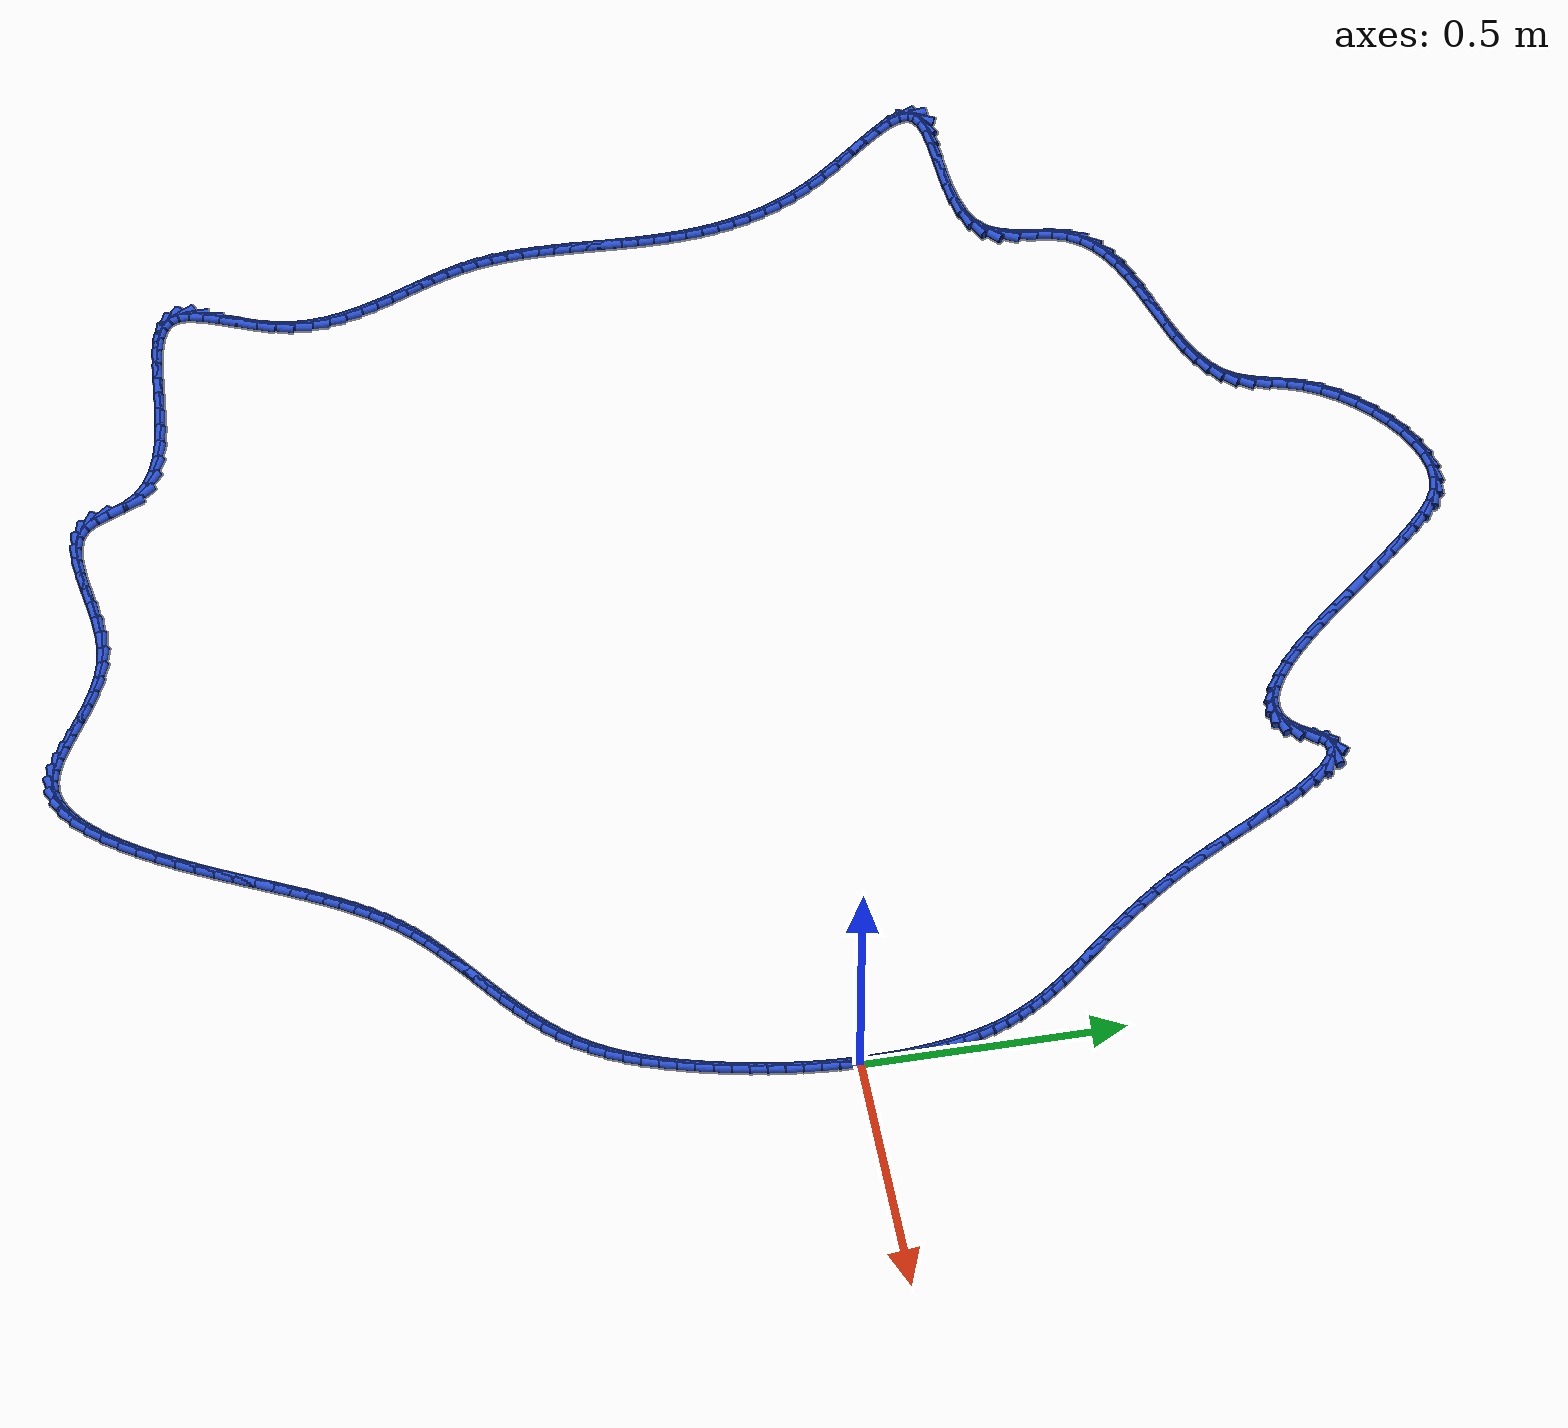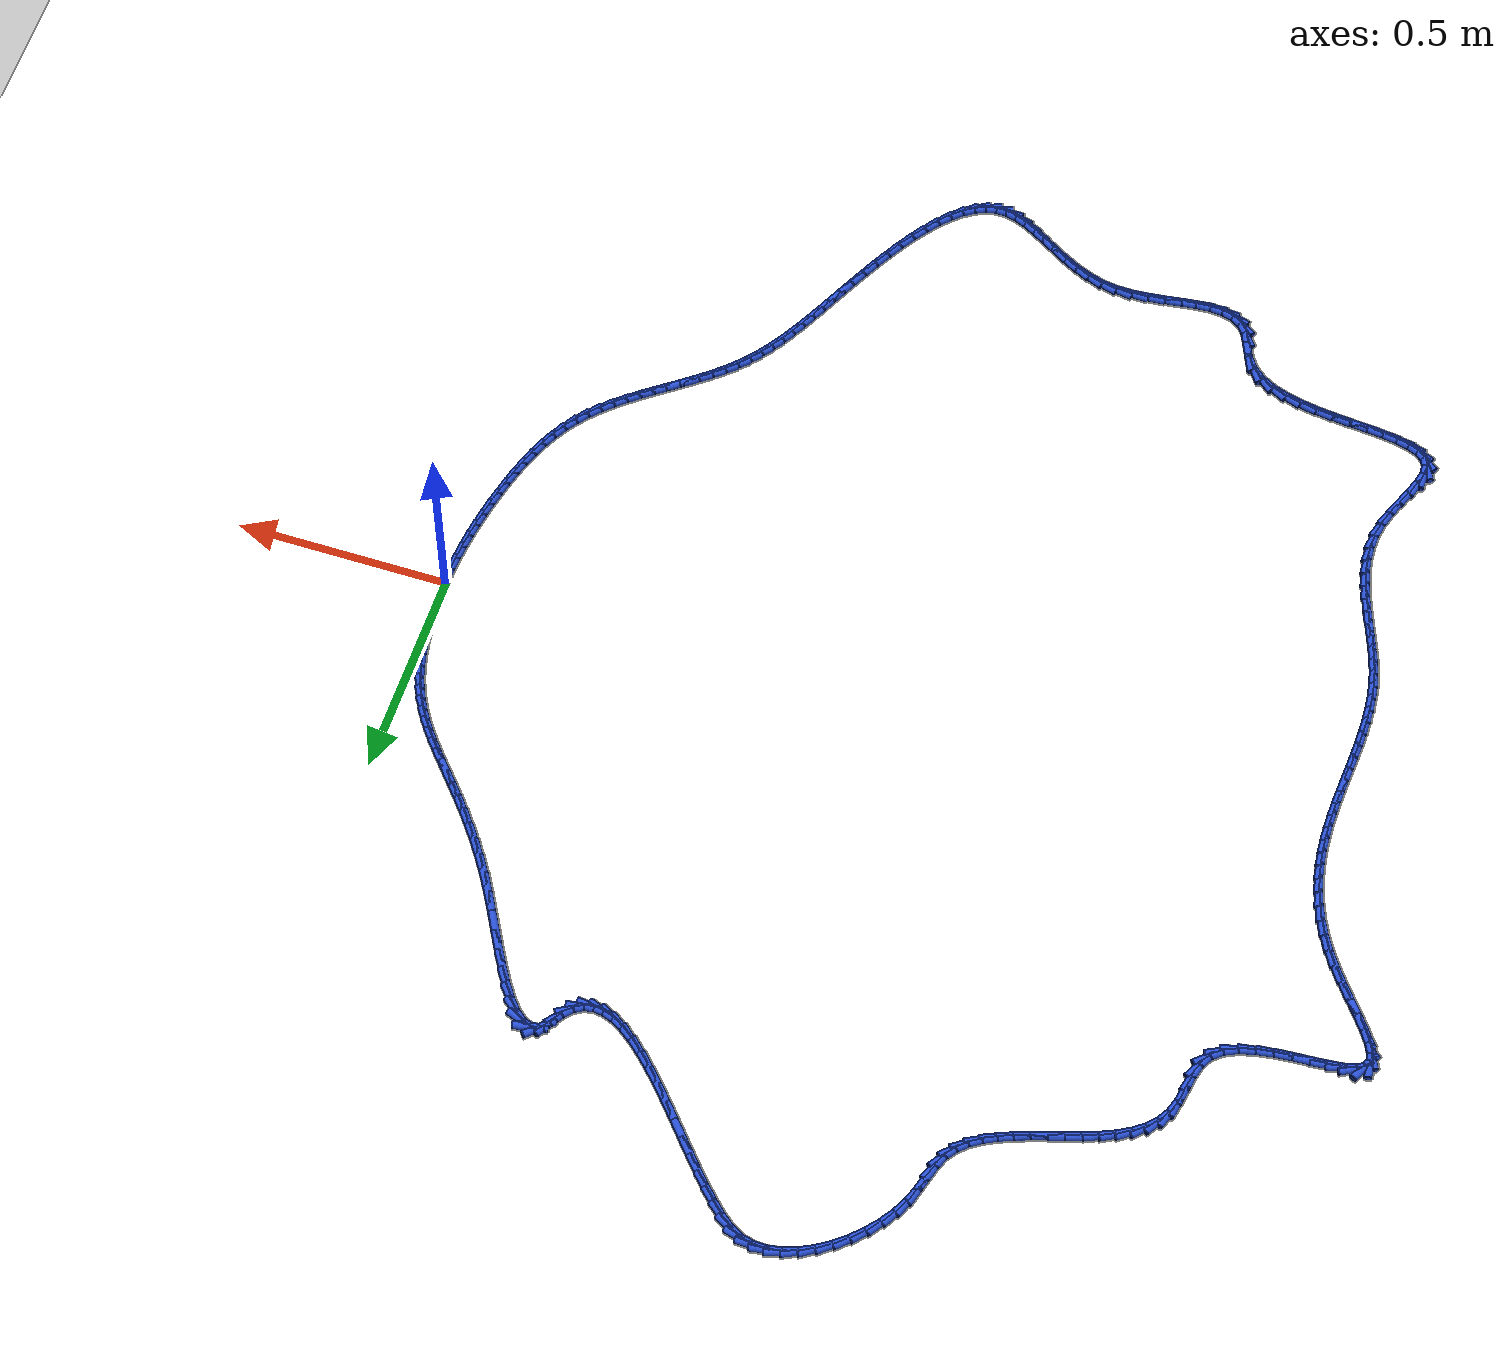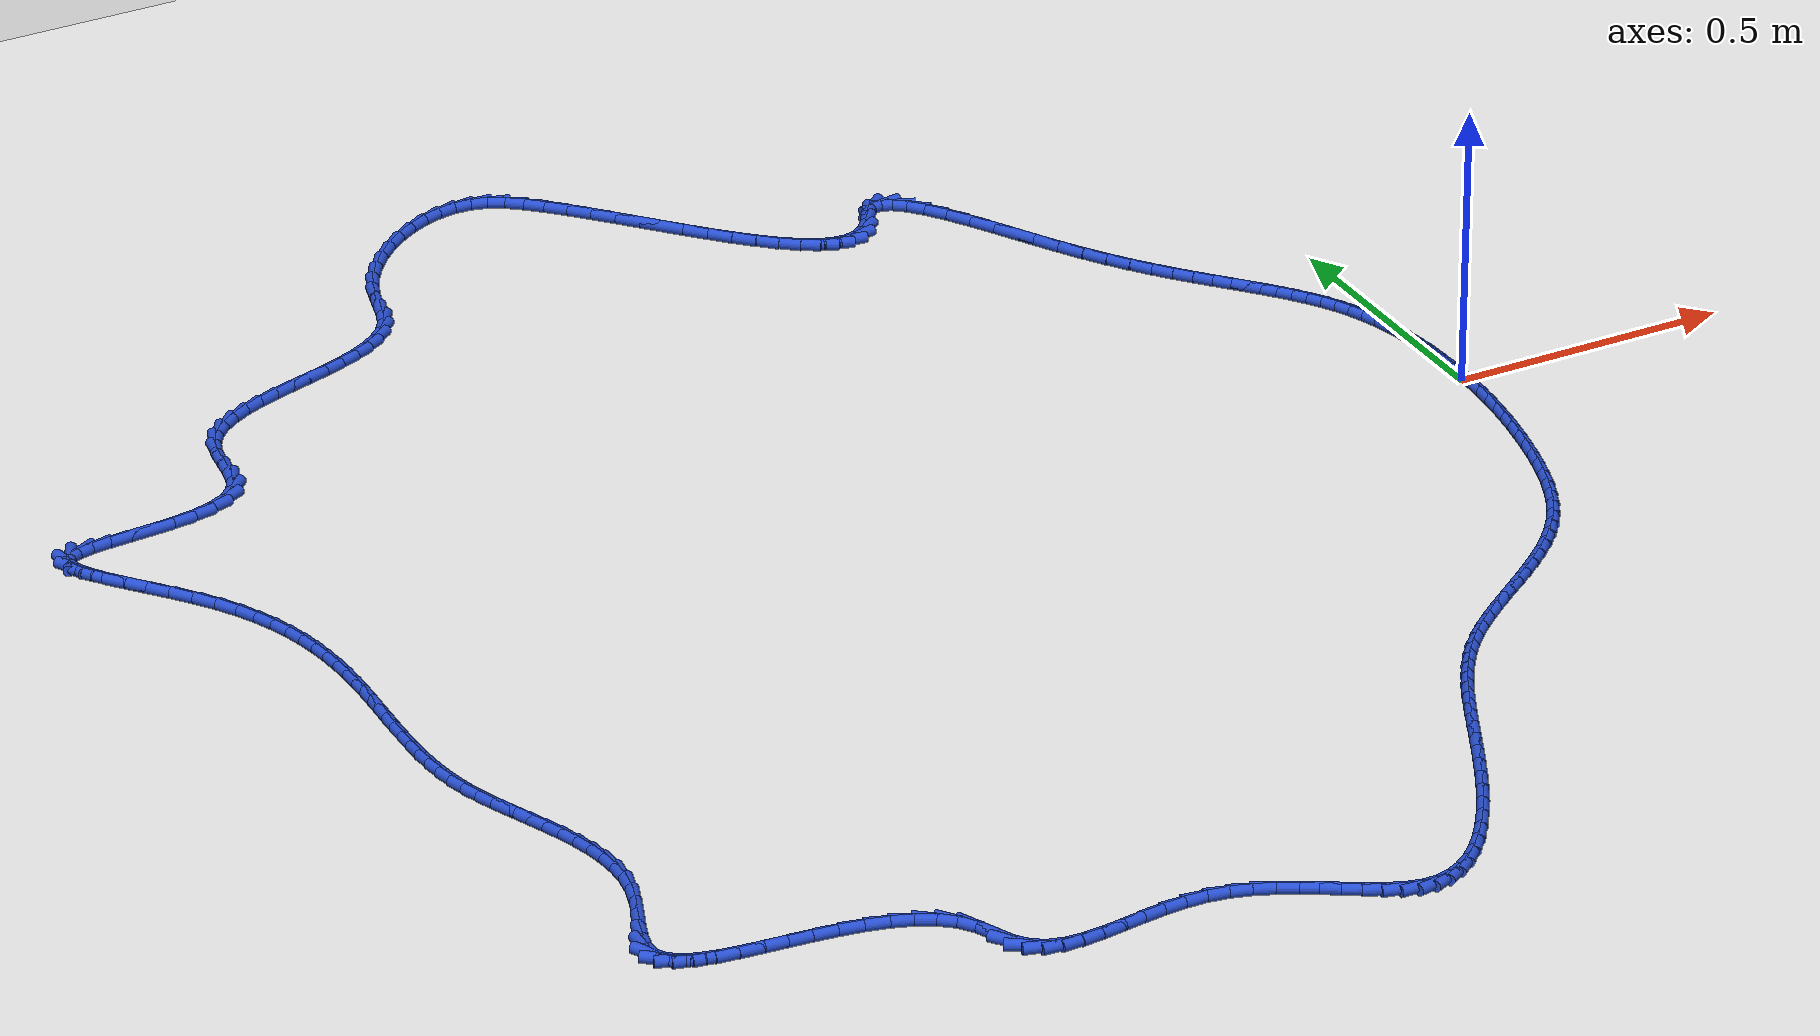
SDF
<sdf version="1.6">
 <world name="default">
  <light name="sun" type="directional">
   <pose>0 0 10 0 -0 0</pose>
   <diffuse>0.8 0.8 0.8 1</diffuse>
   <specular>0.2 0.2 0.2 1</specular>
   <attenuation>
    <range>1000</range>
    <constant>0.9</constant>
    <linear>0.01</linear>
    <quadratic>0.001</quadratic>
   </attenuation>
   <direction>-0.5 0.1 -0.9</direction>
  </light>
  <model name="ground_plane">
   <static>1</static>
   <link name="link">
    <collision name="collision">
     <geometry><plane><normal>0 0 1</normal><size>100 100</size></plane></geometry>
     <surface><friction><ode><mu>100</mu><mu2>50</mu2></ode></friction></surface>
    </collision>
    <visual name="visual">
     <cast_shadows>0</cast_shadows>
     <geometry><plane><normal>0 0 1</normal><size>100 100</size></plane></geometry>
     <material>
      <script><uri>file://media/materials/scripts/gazebo.material</uri><name>Gazebo/WhiteGlow</name></script>
     </material>
    </visual>
   </link>
  </model>
  <gravity>0 0 -9.8</gravity>
  <magnetic_field>6e-06 2.3e-05 -4.2e-05</magnetic_field>
  <atmosphere type="adiabatic"/>
  <physics name="default_physics" default="0" type="ode">
   <max_step_size>0.001</max_step_size>
   <real_time_factor>1</real_time_factor>
   <real_time_update_rate>1000</real_time_update_rate>
  </physics>
  <scene><ambient>0.4 0.4 0.4 1</ambient><background>0.7 0.7 0.7 1</background><shadows>1</shadows></scene>
  <spherical_coordinates>
   <surface_model>EARTH_WGS84</surface_model>
   <latitude_deg>0</latitude_deg>
   <longitude_deg>0</longitude_deg>
   <elevation>0</elevation>
   <heading_deg>0</heading_deg>
  </spherical_coordinates>
  <model name="line">
   <link name="link_0">
    <pose>2.168404344971009e-17 -4.85722573273506e-17 0.01 0 1.57 1.5698805837654344</pose>
    <collision name="collision">
     <geometry><cylinder><radius>0.01</radius><length>0.08</length></cylinder></geometry>
    </collision>
    <visual name="visual">
     <material>
      <script><name>Gazebo/Blue</name><uri>file://media/materials/scripts/gazebo.material</uri></script>
     </material>
     <geometry><cylinder><radius>0.01</radius><length>0.08</length></cylinder></geometry>
    </visual>
   </link>
   <link name="link_1">
    <pose>3.1103723999863517e-05 0.03396554961901245 0.01 0 1.57 -1.5394128594266292</pose>
    <collision name="collision">
     <geometry><cylinder><radius>0.01</radius><length>0.08</length></cylinder></geometry>
    </collision>
    <visual name="visual">
     <material>
      <script><name>Gazebo/Blue</name><uri>file://media/materials/scripts/gazebo.material</uri></script>
     </material>
     <geometry><cylinder><radius>0.01</radius><length>0.08</length></cylinder></geometry>
    </visual>
   </link>
   <link name="link_2">
    <pose>-0.001041612647061923 0.06813526562558116 0.01 0 1.57 -1.50493062476425</pose>
    <collision name="collision">
     <geometry><cylinder><radius>0.01</radius><length>0.08</length></cylinder></geometry>
    </collision>
    <visual name="visual">
     <material>
      <script><name>Gazebo/Blue</name><uri>file://media/materials/scripts/gazebo.material</uri></script>
     </material>
     <geometry><cylinder><radius>0.01</radius><length>0.08</length></cylinder></geometry>
    </visual>
   </link>
   <link name="link_3">
    <pose>-0.003288826881137124 0.10220403791664233 0.01 0 1.57 -1.4674196419176873</pose>
    <collision name="collision">
     <geometry><cylinder><radius>0.01</radius><length>0.08</length></cylinder></geometry>
    </collision>
    <visual name="visual">
     <material>
      <script><name>Gazebo/Blue</name><uri>file://media/materials/scripts/gazebo.material</uri></script>
     </material>
     <geometry><cylinder><radius>0.01</radius><length>0.08</length></cylinder></geometry>
    </visual>
   </link>
   <link name="link_4">
    <pose>-0.006781216746177534 0.13586675638913231 0.01 0 1.57 -1.4259003814461089</pose>
    <collision name="collision">
     <geometry><cylinder><radius>0.01</radius><length>0.08</length></cylinder></geometry>
    </collision>
    <visual name="visual">
     <material>
      <script><name>Gazebo/Blue</name><uri>file://media/materials/scripts/gazebo.material</uri></script>
     </material>
     <geometry><cylinder><radius>0.01</radius><length>0.08</length></cylinder></geometry>
    </visual>
   </link>
   <link name="link_5">
    <pose>-0.011589460010134932 0.1688183109399874 0.01 0 1.57 -1.3791968167658442</pose>
    <collision name="collision">
     <geometry><cylinder><radius>0.01</radius><length>0.08</length></cylinder></geometry>
    </collision>
    <visual name="visual">
     <material>
      <script><name>Gazebo/Blue</name><uri>file://media/materials/scripts/gazebo.material</uri></script>
     </material>
     <geometry><cylinder><radius>0.01</radius><length>0.08</length></cylinder></geometry>
    </visual>
   </link>
   <link name="link_6">
    <pose>-0.017784234440961125 0.20075359146614397 0.01 0 1.57 -1.3258634944821102</pose>
    <collision name="collision">
     <geometry><cylinder><radius>0.01</radius><length>0.08</length></cylinder></geometry>
    </collision>
    <visual name="visual">
     <material>
      <script><name>Gazebo/Blue</name><uri>file://media/materials/scripts/gazebo.material</uri></script>
     </material>
     <geometry><cylinder><radius>0.01</radius><length>0.08</length></cylinder></geometry>
    </visual>
   </link>
   <link name="link_7">
    <pose>-0.025436217806607875 0.2313674878645382 0.01 0 1.57 -1.264103817456565</pose>
    <collision name="collision">
     <geometry><cylinder><radius>0.01</radius><length>0.08</length></cylinder></geometry>
    </collision>
    <visual name="visual">
     <material>
      <script><name>Gazebo/Blue</name><uri>file://media/materials/scripts/gazebo.material</uri></script>
     </material>
     <geometry><cylinder><radius>0.01</radius><length>0.08</length></cylinder></geometry>
    </visual>
   </link>
   <link name="link_8">
    <pose>-0.03461608350601679 0.2603549068060391 0.01 0 1.57 -1.1942190932518901</pose>
    <collision name="collision">
     <geometry><cylinder><radius>0.01</radius><length>0.08</length></cylinder></geometry>
    </collision>
    <visual name="visual">
     <material>
      <script><name>Gazebo/Blue</name><uri>file://media/materials/scripts/gazebo.material</uri></script>
     </material>
     <geometry><cylinder><radius>0.01</radius><length>0.08</length></cylinder></geometry>
    </visual>
   </link>
   <link name="link_9">
    <pose>-0.04536305266513509 0.28753150961506563 0.01 0 1.57 -1.1244701792396612</pose>
    <collision name="collision">
     <geometry><cylinder><radius>0.01</radius><length>0.08</length></cylinder></geometry>
    </collision>
    <visual name="visual">
     <material>
      <script><name>Gazebo/Blue</name><uri>file://media/materials/scripts/gazebo.material</uri></script>
     </material>
     <geometry><cylinder><radius>0.01</radius><length>0.08</length></cylinder></geometry>
    </visual>
   </link>
   <link name="link_10">
    <pose>-0.057609493409606825 0.31312319814251927 0.01 0 1.57 -1.059163996771727</pose>
    <collision name="collision">
     <geometry><cylinder><radius>0.01</radius><length>0.08</length></cylinder></geometry>
    </collision>
    <visual name="visual">
     <material>
      <script><name>Gazebo/Blue</name><uri>file://media/materials/scripts/gazebo.material</uri></script>
     </material>
     <geometry><cylinder><radius>0.01</radius><length>0.08</length></cylinder></geometry>
    </visual>
   </link>
   <link name="link_11">
    <pose>-0.07126510360305308 0.3374429121343683 0.01 0 1.57 -1.0007654764812122</pose>
    <collision name="collision">
     <geometry><cylinder><radius>0.01</radius><length>0.08</length></cylinder></geometry>
    </collision>
    <visual name="visual">
     <material>
      <script><name>Gazebo/Blue</name><uri>file://media/materials/scripts/gazebo.material</uri></script>
     </material>
     <geometry><cylinder><radius>0.01</radius><length>0.08</length></cylinder></geometry>
    </visual>
   </link>
   <link name="link_12">
    <pose>-0.08623958110909491 0.36080359133658046 0.01 0 1.57 -0.9511785535892167</pose>
    <collision name="collision">
     <geometry><cylinder><radius>0.01</radius><length>0.08</length></cylinder></geometry>
    </collision>
    <visual name="visual">
     <material>
      <script><name>Gazebo/Blue</name><uri>file://media/materials/scripts/gazebo.material</uri></script>
     </material>
     <geometry><cylinder><radius>0.01</radius><length>0.08</length></cylinder></geometry>
    </visual>
   </link>
   <link name="link_13">
    <pose>-0.10244262379135331 0.3835181754951235 0.01 0 1.57 -0.9116063459008434</pose>
    <collision name="collision">
     <geometry><cylinder><radius>0.01</radius><length>0.08</length></cylinder></geometry>
    </collision>
    <visual name="visual">
     <material>
      <script><name>Gazebo/Blue</name><uri>file://media/materials/scripts/gazebo.material</uri></script>
     </material>
     <geometry><cylinder><radius>0.01</radius><length>0.08</length></cylinder></geometry>
    </visual>
   </link>
   <link name="link_14">
    <pose>-0.11978392951344947 0.4058996043559655 0.01 0 1.57 -0.8825611799044851</pose>
    <collision name="collision">
     <geometry><cylinder><radius>0.01</radius><length>0.08</length></cylinder></geometry>
    </collision>
    <visual name="visual">
     <material>
      <script><name>Gazebo/Blue</name><uri>file://media/materials/scripts/gazebo.material</uri></script>
     </material>
     <geometry><cylinder><radius>0.01</radius><length>0.08</length></cylinder></geometry>
    </visual>
   </link>
   <link name="link_15">
    <pose>-0.13817319613900433 0.4282608176650743 0.01 0 1.57 -0.8639728229293671</pose>
    <collision name="collision">
     <geometry><cylinder><radius>0.01</radius><length>0.08</length></cylinder></geometry>
    </collision>
    <visual name="visual">
     <material>
      <script><name>Gazebo/Blue</name><uri>file://media/materials/scripts/gazebo.material</uri></script>
     </material>
     <geometry><cylinder><radius>0.01</radius><length>0.08</length></cylinder></geometry>
    </visual>
   </link>
   <link name="link_16">
    <pose>-0.15752012153163897 0.45091475516841756 0.01 0 1.57 -0.8553333232435137</pose>
    <collision name="collision">
     <geometry><cylinder><radius>0.01</radius><length>0.08</length></cylinder></geometry>
    </collision>
    <visual name="visual">
     <material>
      <script><name>Gazebo/Blue</name><uri>file://media/materials/scripts/gazebo.material</uri></script>
     </material>
     <geometry><cylinder><radius>0.01</radius><length>0.08</length></cylinder></geometry>
    </visual>
   </link>
   <link name="link_17">
    <pose>-0.17773440355497447 0.4741743566119632 0.01 0 1.57 -0.8558349306161223</pose>
    <collision name="collision">
     <geometry><cylinder><radius>0.01</radius><length>0.08</length></cylinder></geometry>
    </collision>
    <visual name="visual">
     <material>
      <script><name>Gazebo/Blue</name><uri>file://media/materials/scripts/gazebo.material</uri></script>
     </material>
     <geometry><cylinder><radius>0.01</radius><length>0.08</length></cylinder></geometry>
    </visual>
   </link>
   <link name="link_18">
    <pose>-0.1987257400726319 0.49835256174167925 0.01 0 1.57 -0.8644817888795824</pose>
    <collision name="collision">
     <geometry><cylinder><radius>0.01</radius><length>0.08</length></cylinder></geometry>
    </collision>
    <visual name="visual">
     <material>
      <script><name>Gazebo/Blue</name><uri>file://media/materials/scripts/gazebo.material</uri></script>
     </material>
     <geometry><cylinder><radius>0.01</radius><length>0.08</length></cylinder></geometry>
    </visual>
   </link>
   <link name="link_19">
    <pose>-0.2204038289482323 0.5237623103035334 0.01 0 1.57 -0.880173486880973</pose>
    <collision name="collision">
     <geometry><cylinder><radius>0.01</radius><length>0.08</length></cylinder></geometry>
    </collision>
    <visual name="visual">
     <material>
      <script><name>Gazebo/Blue</name><uri>file://media/materials/scripts/gazebo.material</uri></script>
     </material>
     <geometry><cylinder><radius>0.01</radius><length>0.08</length></cylinder></geometry>
    </visual>
   </link>
   <link name="link_20">
    <pose>-0.2426783680453967 0.5507165420434936 0.01 0 1.57 -0.9017665942969881</pose>
    <collision name="collision">
     <geometry><cylinder><radius>0.01</radius><length>0.08</length></cylinder></geometry>
    </collision>
    <visual name="visual">
     <material>
      <script><name>Gazebo/Blue</name><uri>file://media/materials/scripts/gazebo.material</uri></script>
     </material>
     <geometry><cylinder><radius>0.01</radius><length>0.08</length></cylinder></geometry>
    </visual>
   </link>
   <link name="link_21">
    <pose>-0.26545905522774627 0.5795281967075279 0.01 0 1.57 -0.9281215996041385</pose>
    <collision name="collision">
     <geometry><cylinder><radius>0.01</radius><length>0.08</length></cylinder></geometry>
    </collision>
    <visual name="visual">
     <material>
      <script><name>Gazebo/Blue</name><uri>file://media/materials/scripts/gazebo.material</uri></script>
     </material>
     <geometry><cylinder><radius>0.01</radius><length>0.08</length></cylinder></geometry>
    </visual>
   </link>
   <link name="link_22">
    <pose>-0.2886555883589019 0.6105102140416039 0.01 0 1.57 -0.9581406306600421</pose>
    <collision name="collision">
     <geometry><cylinder><radius>0.01</radius><length>0.08</length></cylinder></geometry>
    </collision>
    <visual name="visual">
     <material>
      <script><name>Gazebo/Blue</name><uri>file://media/materials/scripts/gazebo.material</uri></script>
     </material>
     <geometry><cylinder><radius>0.01</radius><length>0.08</length></cylinder></geometry>
    </visual>
   </link>
   <link name="link_23">
    <pose>-0.3121776653024848 0.6439755337916894 0.01 0 1.57 -0.9907985003495652</pose>
    <collision name="collision">
     <geometry><cylinder><radius>0.01</radius><length>0.08</length></cylinder></geometry>
    </collision>
    <visual name="visual">
     <material>
      <script><name>Gazebo/Blue</name><uri>file://media/materials/scripts/gazebo.material</uri></script>
     </material>
     <geometry><cylinder><radius>0.01</radius><length>0.08</length></cylinder></geometry>
    </visual>
   </link>
   <link name="link_24">
    <pose>-0.33593498392211596 0.6802370957037526 0.01 0 1.57 -1.0250889291759004</pose>
    <collision name="collision">
     <geometry><cylinder><radius>0.01</radius><length>0.08</length></cylinder></geometry>
    </collision>
    <visual name="visual">
     <material>
      <script><name>Gazebo/Blue</name><uri>file://media/materials/scripts/gazebo.material</uri></script>
     </material>
     <geometry><cylinder><radius>0.01</radius><length>0.08</length></cylinder></geometry>
    </visual>
   </link>
   <link name="link_25">
    <pose>-0.35983714089639923 0.7196007095149861 0.01 0 1.57 -1.0539270115147545</pose>
    <collision name="collision">
     <geometry><cylinder><radius>0.01</radius><length>0.08</length></cylinder></geometry>
    </collision>
    <visual name="visual">
     <material>
      <script><name>Gazebo/Blue</name><uri>file://media/materials/scripts/gazebo.material</uri></script>
     </material>
     <geometry><cylinder><radius>0.01</radius><length>0.08</length></cylinder></geometry>
    </visual>
   </link>
   <link name="link_26">
    <pose>-0.3837846366350533 0.7617312157884388 0.01 0 1.57 -1.0680381899601703</pose>
    <collision name="collision">
     <geometry><cylinder><radius>0.01</radius><length>0.08</length></cylinder></geometry>
    </collision>
    <visual name="visual">
     <material>
      <script><name>Gazebo/Blue</name><uri>file://media/materials/scripts/gazebo.material</uri></script>
     </material>
     <geometry><cylinder><radius>0.01</radius><length>0.08</length></cylinder></geometry>
    </visual>
   </link>
   <link name="link_27">
    <pose>-0.40766178633544176 0.8051529630537889 0.01 0 1.57 -1.0684238044153287</pose>
    <collision name="collision">
     <geometry><cylinder><radius>0.01</radius><length>0.08</length></cylinder></geometry>
    </collision>
    <visual name="visual">
     <material>
      <script><name>Gazebo/Blue</name><uri>file://media/materials/scripts/gazebo.material</uri></script>
     </material>
     <geometry><cylinder><radius>0.01</radius><length>0.08</length></cylinder></geometry>
    </visual>
   </link>
   <link name="link_28">
    <pose>-0.4313512369025209 0.848272743508515 0.01 0 1.57 -1.0548106414781273</pose>
    <collision name="collision">
     <geometry><cylinder><radius>0.01</radius><length>0.08</length></cylinder></geometry>
    </collision>
    <visual name="visual">
     <material>
      <script><name>Gazebo/Blue</name><uri>file://media/materials/scripts/gazebo.material</uri></script>
     </material>
     <geometry><cylinder><radius>0.01</radius><length>0.08</length></cylinder></geometry>
    </visual>
   </link>
   <link name="link_29">
    <pose>-0.4547356352412465 0.8894973493500952 0.01 0 1.57 -1.0241599059915352</pose>
    <collision name="collision">
     <geometry><cylinder><radius>0.01</radius><length>0.08</length></cylinder></geometry>
    </collision>
    <visual name="visual">
     <material>
      <script><name>Gazebo/Blue</name><uri>file://media/materials/scripts/gazebo.material</uri></script>
     </material>
     <geometry><cylinder><radius>0.01</radius><length>0.08</length></cylinder></geometry>
    </visual>
   </link>
   <link name="link_30">
    <pose>-0.47769762825657447 0.9272335727760074 0.01 0 1.57 -0.9690878401755821</pose>
    <collision name="collision">
     <geometry><cylinder><radius>0.01</radius><length>0.08</length></cylinder></geometry>
    </collision>
    <visual name="visual">
     <material>
      <script><name>Gazebo/Blue</name><uri>file://media/materials/scripts/gazebo.material</uri></script>
     </material>
     <geometry><cylinder><radius>0.01</radius><length>0.08</length></cylinder></geometry>
    </visual>
   </link>
   <link name="link_31">
    <pose>-0.5001198628534606 0.9598882059837297 0.01 0 1.57 -0.87344547445641</pose>
    <collision name="collision">
     <geometry><cylinder><radius>0.01</radius><length>0.08</length></cylinder></geometry>
    </collision>
    <visual name="visual">
     <material>
      <script><name>Gazebo/Blue</name><uri>file://media/materials/scripts/gazebo.material</uri></script>
     </material>
     <geometry><cylinder><radius>0.01</radius><length>0.08</length></cylinder></geometry>
    </visual>
   </link>
   <link name="link_32">
    <pose>-0.5218849859368613 0.9858680411707408 0.01 0 1.57 -0.7008811582731305</pose>
    <collision name="collision">
     <geometry><cylinder><radius>0.01</radius><length>0.08</length></cylinder></geometry>
    </collision>
    <visual name="visual">
     <material>
      <script><name>Gazebo/Blue</name><uri>file://media/materials/scripts/gazebo.material</uri></script>
     </material>
     <geometry><cylinder><radius>0.01</radius><length>0.08</length></cylinder></geometry>
    </visual>
   </link>
   <link name="link_33">
    <pose>-0.5428756444117322 1.0035798705345185 0.01 0 1.57 -0.37237712451530136</pose>
    <collision name="collision">
     <geometry><cylinder><radius>0.01</radius><length>0.08</length></cylinder></geometry>
    </collision>
    <visual name="visual">
     <material>
      <script><name>Gazebo/Blue</name><uri>file://media/materials/scripts/gazebo.material</uri></script>
     </material>
     <geometry><cylinder><radius>0.01</radius><length>0.08</length></cylinder></geometry>
    </visual>
   </link>
   <link name="link_34">
    <pose>-0.5629744851830292 1.0114304862725407 0.01 0 1.57 0.18658711430496422</pose>
    <collision name="collision">
     <geometry><cylinder><radius>0.01</radius><length>0.08</length></cylinder></geometry>
    </collision>
    <visual name="visual">
     <material>
      <script><name>Gazebo/Blue</name><uri>file://media/materials/scripts/gazebo.material</uri></script>
     </material>
     <geometry><cylinder><radius>0.01</radius><length>0.08</length></cylinder></geometry>
    </visual>
   </link>
   <link name="link_35">
    <pose>-0.5820641551557083 1.0078266805822857 0.01 0 1.57 0.7475215292573569</pose>
    <collision name="collision">
     <geometry><cylinder><radius>0.01</radius><length>0.08</length></cylinder></geometry>
    </collision>
    <visual name="visual">
     <material>
      <script><name>Gazebo/Blue</name><uri>file://media/materials/scripts/gazebo.material</uri></script>
     </material>
     <geometry><cylinder><radius>0.01</radius><length>0.08</length></cylinder></geometry>
    </visual>
   </link>
   <link name="link_36">
    <pose>-0.6000273012347255 0.9911752456612324 0.01 0 1.57 1.0104329750895307</pose>
    <collision name="collision">
     <geometry><cylinder><radius>0.01</radius><length>0.08</length></cylinder></geometry>
    </collision>
    <visual name="visual">
     <material>
      <script><name>Gazebo/Blue</name><uri>file://media/materials/scripts/gazebo.material</uri></script>
     </material>
     <geometry><cylinder><radius>0.01</radius><length>0.08</length></cylinder></geometry>
    </visual>
   </link>
   <link name="link_37">
    <pose>-0.6172555578836 0.9637179235494869 0.01 0 1.57 0.8541976067570057</pose>
    <collision name="collision">
     <geometry><cylinder><radius>0.01</radius><length>0.08</length></cylinder></geometry>
    </collision>
    <visual name="visual">
     <material>
      <script><name>Gazebo/Blue</name><uri>file://media/materials/scripts/gazebo.material</uri></script>
     </material>
     <geometry><cylinder><radius>0.01</radius><length>0.08</length></cylinder></geometry>
    </visual>
   </link>
   <link name="link_38">
    <pose>-0.6360230160107025 0.942172583022034 0.01 0 1.57 0.5500863840229262</pose>
    <collision name="collision">
     <geometry><cylinder><radius>0.01</radius><length>0.08</length></cylinder></geometry>
    </collision>
    <visual name="visual">
     <material>
      <script><name>Gazebo/Blue</name><uri>file://media/materials/scripts/gazebo.material</uri></script>
     </material>
     <geometry><cylinder><radius>0.01</radius><length>0.08</length></cylinder></geometry>
    </visual>
   </link>
   <link name="link_39">
    <pose>-0.656670785221348 0.9295108738431355 0.01 0 1.57 0.2004663293223428</pose>
    <collision name="collision">
     <geometry><cylinder><radius>0.01</radius><length>0.08</length></cylinder></geometry>
    </collision>
    <visual name="visual">
     <material>
      <script><name>Gazebo/Blue</name><uri>file://media/materials/scripts/gazebo.material</uri></script>
     </material>
     <geometry><cylinder><radius>0.01</radius><length>0.08</length></cylinder></geometry>
    </visual>
   </link>
   <link name="link_40">
    <pose>-0.6790254447408911 0.9249685059957651 0.01 0 1.57 -0.11720434471533314</pose>
    <collision name="collision">
     <geometry><cylinder><radius>0.01</radius><length>0.08</length></cylinder></geometry>
    </collision>
    <visual name="visual">
     <material>
      <script><name>Gazebo/Blue</name><uri>file://media/materials/scripts/gazebo.material</uri></script>
     </material>
     <geometry><cylinder><radius>0.01</radius><length>0.08</length></cylinder></geometry>
    </visual>
   </link>
   <link name="link_41">
    <pose>-0.7029135737946874 0.9277811894628979 0.01 0 1.57 -0.3565248666928859</pose>
    <collision name="collision">
     <geometry><cylinder><radius>0.01</radius><length>0.08</length></cylinder></geometry>
    </collision>
    <visual name="visual">
     <material>
      <script><name>Gazebo/Blue</name><uri>file://media/materials/scripts/gazebo.material</uri></script>
     </material>
     <geometry><cylinder><radius>0.01</radius><length>0.08</length></cylinder></geometry>
    </visual>
   </link>
   <link name="link_42">
    <pose>-0.7281617516080922 0.9371846342275075 0.01 0 1.57 -0.5226839813775308</pose>
    <collision name="collision">
     <geometry><cylinder><radius>0.01</radius><length>0.08</length></cylinder></geometry>
    </collision>
    <visual name="visual">
     <material>
      <script><name>Gazebo/Blue</name><uri>file://media/materials/scripts/gazebo.material</uri></script>
     </material>
     <geometry><cylinder><radius>0.01</radius><length>0.08</length></cylinder></geometry>
    </visual>
   </link>
   <link name="link_43">
    <pose>-0.7545965574064611 0.9524145502725689 0.01 0 1.57 -0.636612712445648</pose>
    <collision name="collision">
     <geometry><cylinder><radius>0.01</radius><length>0.08</length></cylinder></geometry>
    </collision>
    <visual name="visual">
     <material>
      <script><name>Gazebo/Blue</name><uri>file://media/materials/scripts/gazebo.material</uri></script>
     </material>
     <geometry><cylinder><radius>0.01</radius><length>0.08</length></cylinder></geometry>
    </visual>
   </link>
   <link name="link_44">
    <pose>-0.7820445704151485 0.972706647581056 0.01 0 1.57 -0.7155805565808642</pose>
    <collision name="collision">
     <geometry><cylinder><radius>0.01</radius><length>0.08</length></cylinder></geometry>
    </collision>
    <visual name="visual">
     <material>
      <script><name>Gazebo/Blue</name><uri>file://media/materials/scripts/gazebo.material</uri></script>
     </material>
     <geometry><cylinder><radius>0.01</radius><length>0.08</length></cylinder></geometry>
    </visual>
   </link>
   <link name="link_45">
    <pose>-0.810332369859511 0.9972966361359433 0.01 0 1.57 -0.7708475437157227</pose>
    <collision name="collision">
     <geometry><cylinder><radius>0.01</radius><length>0.08</length></cylinder></geometry>
    </collision>
    <visual name="visual">
     <material>
      <script><name>Gazebo/Blue</name><uri>file://media/materials/scripts/gazebo.material</uri></script>
     </material>
     <geometry><cylinder><radius>0.01</radius><length>0.08</length></cylinder></geometry>
    </visual>
   </link>
   <link name="link_46">
    <pose>-0.8392865349649027 1.025420225920205 0.01 0 1.57 -0.8093543144175936</pose>
    <collision name="collision">
     <geometry><cylinder><radius>0.01</radius><length>0.08</length></cylinder></geometry>
    </collision>
    <visual name="visual">
     <material>
      <script><name>Gazebo/Blue</name><uri>file://media/materials/scripts/gazebo.material</uri></script>
     </material>
     <geometry><cylinder><radius>0.01</radius><length>0.08</length></cylinder></geometry>
    </visual>
   </link>
   <link name="link_47">
    <pose>-0.86873364495668 1.056313126916816 0.01 0 1.57 -0.8353256821414923</pose>
    <collision name="collision">
     <geometry><cylinder><radius>0.01</radius><length>0.08</length></cylinder></geometry>
    </collision>
    <visual name="visual">
     <material>
      <script><name>Gazebo/Blue</name><uri>file://media/materials/scripts/gazebo.material</uri></script>
     </material>
     <geometry><cylinder><radius>0.01</radius><length>0.08</length></cylinder></geometry>
    </visual>
   </link>
   <link name="link_48">
    <pose>-0.8985002790601978 1.0892110491087503 0.01 0 1.57 -0.8512796391164228</pose>
    <collision name="collision">
     <geometry><cylinder><radius>0.01</radius><length>0.08</length></cylinder></geometry>
    </collision>
    <visual name="visual">
     <material>
      <script><name>Gazebo/Blue</name><uri>file://media/materials/scripts/gazebo.material</uri></script>
     </material>
     <geometry><cylinder><radius>0.01</radius><length>0.08</length></cylinder></geometry>
    </visual>
   </link>
   <link name="link_49">
    <pose>-0.9284130165008108 1.1233497024789816 0.01 0 1.57 -0.8585948615771395</pose>
    <collision name="collision">
     <geometry><cylinder><radius>0.01</radius><length>0.08</length></cylinder></geometry>
    </collision>
    <visual name="visual">
     <material>
      <script><name>Gazebo/Blue</name><uri>file://media/materials/scripts/gazebo.material</uri></script>
     </material>
     <geometry><cylinder><radius>0.01</radius><length>0.08</length></cylinder></geometry>
    </visual>
   </link>
   <link name="link_50">
    <pose>-0.9582984365038754 1.1579647970104854 0.01 0 1.57 -0.8577979417933926</pose>
    <collision name="collision">
     <geometry><cylinder><radius>0.01</radius><length>0.08</length></cylinder></geometry>
    </collision>
    <visual name="visual">
     <material>
      <script><name>Gazebo/Blue</name><uri>file://media/materials/scripts/gazebo.material</uri></script>
     </material>
     <geometry><cylinder><radius>0.01</radius><length>0.08</length></cylinder></geometry>
    </visual>
   </link>
   <link name="link_51">
    <pose>-0.987983118294746 1.192292042686235 0.01 0 1.57 -0.8486601893002543</pose>
    <collision name="collision">
     <geometry><cylinder><radius>0.01</radius><length>0.08</length></cylinder></geometry>
    </collision>
    <visual name="visual">
     <material>
      <script><name>Gazebo/Blue</name><uri>file://media/materials/scripts/gazebo.material</uri></script>
     </material>
     <geometry><cylinder><radius>0.01</radius><length>0.08</length></cylinder></geometry>
    </visual>
   </link>
   <link name="link_52">
    <pose>-1.017293641098779 1.2255671494892055 0.01 0 1.57 -0.8301318726310187</pose>
    <collision name="collision">
     <geometry><cylinder><radius>0.01</radius><length>0.08</length></cylinder></geometry>
    </collision>
    <visual name="visual">
     <material>
      <script><name>Gazebo/Blue</name><uri>file://media/materials/scripts/gazebo.material</uri></script>
     </material>
     <geometry><cylinder><radius>0.01</radius><length>0.08</length></cylinder></geometry>
    </visual>
   </link>
   <link name="link_53">
    <pose>-1.0460565841413283 1.257025827402371 0.01 0 1.57 -0.8000847030574295</pose>
    <collision name="collision">
     <geometry><cylinder><radius>0.01</radius><length>0.08</length></cylinder></geometry>
    </collision>
    <visual name="visual">
     <material>
      <script><name>Gazebo/Blue</name><uri>file://media/materials/scripts/gazebo.material</uri></script>
     </material>
     <geometry><cylinder><radius>0.01</radius><length>0.08</length></cylinder></geometry>
    </visual>
   </link>
   <link name="link_54">
    <pose>-1.0740985266477505 1.2859037864087057 0.01 0 1.57 -0.7547426580482212</pose>
    <collision name="collision">
     <geometry><cylinder><radius>0.01</radius><length>0.08</length></cylinder></geometry>
    </collision>
    <visual name="visual">
     <material>
      <script><name>Gazebo/Blue</name><uri>file://media/materials/scripts/gazebo.material</uri></script>
     </material>
     <geometry><cylinder><radius>0.01</radius><length>0.08</length></cylinder></geometry>
    </visual>
   </link>
   <link name="link_55">
    <pose>-1.101246624327494 1.3114364234628753 0.01 0 1.57 -0.6736233895597995</pose>
    <collision name="collision">
     <geometry><cylinder><radius>0.01</radius><length>0.08</length></cylinder></geometry>
    </collision>
    <visual name="visual">
     <material>
      <script><name>Gazebo/Blue</name><uri>file://media/materials/scripts/gazebo.material</uri></script>
     </material>
     <geometry><cylinder><radius>0.01</radius><length>0.08</length></cylinder></geometry>
    </visual>
   </link>
   <link name="link_56">
    <pose>-1.1277793900611097 1.3326140505756454 0.01 0 1.57 -0.5036618672845306</pose>
    <collision name="collision">
     <geometry><cylinder><radius>0.01</radius><length>0.08</length></cylinder></geometry>
    </collision>
    <visual name="visual">
     <material>
      <script><name>Gazebo/Blue</name><uri>file://media/materials/scripts/gazebo.material</uri></script>
     </material>
     <geometry><cylinder><radius>0.01</radius><length>0.08</length></cylinder></geometry>
    </visual>
   </link>
   <link name="link_57">
    <pose>-1.1552344455231465 1.3477436195968044 0.01 0 1.57 -0.2592143617377638</pose>
    <collision name="collision">
     <geometry><cylinder><radius>0.01</radius><length>0.08</length></cylinder></geometry>
    </collision>
    <visual name="visual">
     <material>
      <script><name>Gazebo/Blue</name><uri>file://media/materials/scripts/gazebo.material</uri></script>
     </material>
     <geometry><cylinder><radius>0.01</radius><length>0.08</length></cylinder></geometry>
    </visual>
   </link>
   <link name="link_58">
    <pose>-1.1848035570198805 1.355584770819409 0.01 0 1.57 -0.029114231427330307</pose>
    <collision name="collision">
     <geometry><cylinder><radius>0.01</radius><length>0.08</length></cylinder></geometry>
    </collision>
    <visual name="visual">
     <material>
      <script><name>Gazebo/Blue</name><uri>file://media/materials/scripts/gazebo.material</uri></script>
     </material>
     <geometry><cylinder><radius>0.01</radius><length>0.08</length></cylinder></geometry>
    </visual>
   </link>
   <link name="link_59">
    <pose>-1.2160995093490654 1.3564961859496556 0.01 0 1.57 0.16479844236933405</pose>
    <collision name="collision">
     <geometry><cylinder><radius>0.01</radius><length>0.08</length></cylinder></geometry>
    </collision>
    <visual name="visual">
     <material>
      <script><name>Gazebo/Blue</name><uri>file://media/materials/scripts/gazebo.material</uri></script>
     </material>
     <geometry><cylinder><radius>0.01</radius><length>0.08</length></cylinder></geometry>
    </visual>
   </link>
   <link name="link_60">
    <pose>-1.2484608388915135 1.3511142792534978 0.01 0 1.57 0.32496269955815726</pose>
    <collision name="collision">
     <geometry><cylinder><radius>0.01</radius><length>0.08</length></cylinder></geometry>
    </collision>
    <visual name="visual">
     <material>
      <script><name>Gazebo/Blue</name><uri>file://media/materials/scripts/gazebo.material</uri></script>
     </material>
     <geometry><cylinder><radius>0.01</radius><length>0.08</length></cylinder></geometry>
    </visual>
   </link>
   <link name="link_61">
    <pose>-1.2812260820280374 1.340075464996889 0.01 0 1.57 0.4588486390109197</pose>
    <collision name="collision">
     <geometry><cylinder><radius>0.01</radius><length>0.08</length></cylinder></geometry>
    </collision>
    <visual name="visual">
     <material>
      <script><name>Gazebo/Blue</name><uri>file://media/materials/scripts/gazebo.material</uri></script>
     </material>
     <geometry><cylinder><radius>0.01</radius><length>0.08</length></cylinder></geometry>
    </visual>
   </link>
   <link name="link_62">
    <pose>-1.3137337751394498 1.3240161574457836 0.01 0 1.57 0.5743863355615457</pose>
    <collision name="collision">
     <geometry><cylinder><radius>0.01</radius><length>0.08</length></cylinder></geometry>
    </collision>
    <visual name="visual">
     <material>
      <script><name>Gazebo/Blue</name><uri>file://media/materials/scripts/gazebo.material</uri></script>
     </material>
     <geometry><cylinder><radius>0.01</radius><length>0.08</length></cylinder></geometry>
    </visual>
   </link>
   <link name="link_63">
    <pose>-1.3453224546065645 1.303572770866135 0.01 0 1.57 0.6784784791155526</pose>
    <collision name="collision">
     <geometry><cylinder><radius>0.01</radius><length>0.08</length></cylinder></geometry>
    </collision>
    <visual name="visual">
     <material>
      <script><name>Gazebo/Blue</name><uri>file://media/materials/scripts/gazebo.material</uri></script>
     </material>
     <geometry><cylinder><radius>0.01</radius><length>0.08</length></cylinder></geometry>
    </visual>
   </link>
   <link name="link_64">
    <pose>-1.375330656810193 1.2793817195238983 0.01 0 1.57 0.7769732385723196</pose>
    <collision name="collision">
     <geometry><cylinder><radius>0.01</radius><length>0.08</length></cylinder></geometry>
    </collision>
    <visual name="visual">
     <material>
      <script><name>Gazebo/Blue</name><uri>file://media/materials/scripts/gazebo.material</uri></script>
     </material>
     <geometry><cylinder><radius>0.01</radius><length>0.08</length></cylinder></geometry>
    </visual>
   </link>
   <link name="link_65">
    <pose>-1.4030969181311483 1.2520794176850265 0.01 0 1.57 0.8750960951735991</pose>
    <collision name="collision">
     <geometry><cylinder><radius>0.01</radius><length>0.08</length></cylinder></geometry>
    </collision>
    <visual name="visual">
     <material>
      <script><name>Gazebo/Blue</name><uri>file://media/materials/scripts/gazebo.material</uri></script>
     </material>
     <geometry><cylinder><radius>0.01</radius><length>0.08</length></cylinder></geometry>
    </visual>
   </link>
   <link name="link_66">
    <pose>-1.427959774950244 1.2223022796154734 0.01 0 1.57 0.9779710510233154</pose>
    <collision name="collision">
     <geometry><cylinder><radius>0.01</radius><length>0.08</length></cylinder></geometry>
    </collision>
    <visual name="visual">
     <material>
      <script><name>Gazebo/Blue</name><uri>file://media/materials/scripts/gazebo.material</uri></script>
     </material>
     <geometry><cylinder><radius>0.01</radius><length>0.08</length></cylinder></geometry>
    </visual>
   </link>
   <link name="link_67">
    <pose>-1.4492577636482915 1.190686719581194 0.01 0 1.57 1.0911206188467832</pose>
    <collision name="collision">
     <geometry><cylinder><radius>0.01</radius><length>0.08</length></cylinder></geometry>
    </collision>
    <visual name="visual">
     <material>
      <script><name>Gazebo/Blue</name><uri>file://media/materials/scripts/gazebo.material</uri></script>
     </material>
     <geometry><cylinder><radius>0.01</radius><length>0.08</length></cylinder></geometry>
    </visual>
   </link>
   <link name="link_68">
    <pose>-1.466329420606105 1.1578691518481417 0.01 0 1.57 1.216204776297123</pose>
    <collision name="collision">
     <geometry><cylinder><radius>0.01</radius><length>0.08</length></cylinder></geometry>
    </collision>
    <visual name="visual">
     <material>
      <script><name>Gazebo/Blue</name><uri>file://media/materials/scripts/gazebo.material</uri></script>
     </material>
     <geometry><cylinder><radius>0.01</radius><length>0.08</length></cylinder></geometry>
    </visual>
   </link>
   <link name="link_69">
    <pose>-1.4786794836276835 1.1245122961461333 0.01 0 1.57 1.2989064659948744</pose>
    <collision name="collision">
     <geometry><cylinder><radius>0.01</radius><length>0.08</length></cylinder></geometry>
    </collision>
    <visual name="visual">
     <material>
      <script><name>Gazebo/Blue</name><uri>file://media/materials/scripts/gazebo.material</uri></script>
     </material>
     <geometry><cylinder><radius>0.01</radius><length>0.08</length></cylinder></geometry>
    </visual>
   </link>
   <link name="link_70">
    <pose>-1.487854653164944 1.0916020630273882 0.01 0 1.57 1.2928845797492947</pose>
    <collision name="collision">
     <geometry><cylinder><radius>0.01</radius><length>0.08</length></cylinder></geometry>
    </collision>
    <visual name="visual">
     <material>
      <script><name>Gazebo/Blue</name><uri>file://media/materials/scripts/gazebo.material</uri></script>
     </material>
     <geometry><cylinder><radius>0.01</radius><length>0.08</length></cylinder></geometry>
    </visual>
   </link>
   <link name="link_71">
    <pose>-1.4967731451730233 1.0603414391125232 0.01 0 1.57 1.1829111299774673</pose>
    <collision name="collision">
     <geometry><cylinder><radius>0.01</radius><length>0.08</length></cylinder></geometry>
    </collision>
    <visual name="visual">
     <material>
      <script><name>Gazebo/Blue</name><uri>file://media/materials/scripts/gazebo.material</uri></script>
     </material>
     <geometry><cylinder><radius>0.01</radius><length>0.08</length></cylinder></geometry>
    </visual>
   </link>
   <link name="link_72">
    <pose>-1.5083785934705554 1.0319374340243461 0.01 0 1.57 0.9725657130226586</pose>
    <collision name="collision">
     <geometry><cylinder><radius>0.01</radius><length>0.08</length></cylinder></geometry>
    </collision>
    <visual name="visual">
     <material>
      <script><name>Gazebo/Blue</name><uri>file://media/materials/scripts/gazebo.material</uri></script>
     </material>
     <geometry><cylinder><radius>0.01</radius><length>0.08</length></cylinder></geometry>
    </visual>
   </link>
   <link name="link_73">
    <pose>-1.525126243808694 1.0073642745656446 0.01 0 1.57 0.7636749871799272</pose>
    <collision name="collision">
     <geometry><cylinder><radius>0.01</radius><length>0.08</length></cylinder></geometry>
    </collision>
    <visual name="visual">
     <material>
      <script><name>Gazebo/Blue</name><uri>file://media/materials/scripts/gazebo.material</uri></script>
     </material>
     <geometry><cylinder><radius>0.01</radius><length>0.08</length></cylinder></geometry>
    </visual>
   </link>
   <link name="link_74">
    <pose>-1.5470017652410109 0.9864191009840713 0.01 0 1.57 0.598954644999353</pose>
    <collision name="collision">
     <geometry><cylinder><radius>0.01</radius><length>0.08</length></cylinder></geometry>
    </collision>
    <visual name="visual">
     <material>
      <script><name>Gazebo/Blue</name><uri>file://media/materials/scripts/gazebo.material</uri></script>
     </material>
     <geometry><cylinder><radius>0.01</radius><length>0.08</length></cylinder></geometry>
    </visual>
   </link>
   <link name="link_75">
    <pose>-1.5732120615632186 0.9685278667908941 0.01 0 1.57 0.47794662828195617</pose>
    <collision name="collision">
     <geometry><cylinder><radius>0.01</radius><length>0.08</length></cylinder></geometry>
    </collision>
    <visual name="visual">
     <material>
      <script><name>Gazebo/Blue</name><uri>file://media/materials/scripts/gazebo.material</uri></script>
     </material>
     <geometry><cylinder><radius>0.01</radius><length>0.08</length></cylinder></geometry>
    </visual>
   </link>
   <link name="link_76">
    <pose>-1.6029637425895902 0.9531163853755519 0.01 0 1.57 0.39385697624293586</pose>
    <collision name="collision">
     <geometry><cylinder><radius>0.01</radius><length>0.08</length></cylinder></geometry>
    </collision>
    <visual name="visual">
     <material>
      <script><name>Gazebo/Blue</name><uri>file://media/materials/scripts/gazebo.material</uri></script>
     </material>
     <geometry><cylinder><radius>0.01</radius><length>0.08</length></cylinder></geometry>
    </visual>
   </link>
   <link name="link_77">
    <pose>-1.6354634181343974 0.9396104701274834 0.01 0 1.57 0.3396590966669234</pose>
    <collision name="collision">
     <geometry><cylinder><radius>0.01</radius><length>0.08</length></cylinder></geometry>
    </collision>
    <visual name="visual">
     <material>
      <script><name>Gazebo/Blue</name><uri>file://media/materials/scripts/gazebo.material</uri></script>
     </material>
     <geometry><cylinder><radius>0.01</radius><length>0.08</length></cylinder></geometry>
    </visual>
   </link>
   <link name="link_78">
    <pose>-1.6699176980119135 0.9274359344361278 0.01 0 1.57 0.3102220469603327</pose>
    <collision name="collision">
     <geometry><cylinder><radius>0.01</radius><length>0.08</length></cylinder></geometry>
    </collision>
    <visual name="visual">
     <material>
      <script><name>Gazebo/Blue</name><uri>file://media/materials/scripts/gazebo.material</uri></script>
     </material>
     <geometry><cylinder><radius>0.01</radius><length>0.08</length></cylinder></geometry>
    </visual>
   </link>
   <link name="link_79">
    <pose>-1.7055331920364096 0.9160185916909241 0.01 0 1.57 0.302620259878519</pose>
    <collision name="collision">
     <geometry><cylinder><radius>0.01</radius><length>0.08</length></cylinder></geometry>
    </collision>
    <visual name="visual">
     <material>
      <script><name>Gazebo/Blue</name><uri>file://media/materials/scripts/gazebo.material</uri></script>
     </material>
     <geometry><cylinder><radius>0.01</radius><length>0.08</length></cylinder></geometry>
    </visual>
   </link>
   <link name="link_80">
    <pose>-1.741516510022159 0.9047842552813116 0.01 0 1.57 0.3159923020732963</pose>
    <collision name="collision">
     <geometry><cylinder><radius>0.01</radius><length>0.08</length></cylinder></geometry>
    </collision>
    <visual name="visual">
     <material>
      <script><name>Gazebo/Blue</name><uri>file://media/materials/scripts/gazebo.material</uri></script>
     </material>
     <geometry><cylinder><radius>0.01</radius><length>0.08</length></cylinder></geometry>
    </visual>
   </link>
   <link name="link_81">
    <pose>-1.7770742617834347 0.8931587385967289 0.01 0 1.57 0.3514445871361449</pose>
    <collision name="collision">
     <geometry><cylinder><radius>0.01</radius><length>0.08</length></cylinder></geometry>
    </collision>
    <visual name="visual">
     <material>
      <script><name>Gazebo/Blue</name><uri>file://media/materials/scripts/gazebo.material</uri></script>
     </material>
     <geometry><cylinder><radius>0.01</radius><length>0.08</length></cylinder></geometry>
    </visual>
   </link>
   <link name="link_82">
    <pose>-1.8114130571345077 0.8805678550266156 0.01 0 1.57 0.4120888435364971</pose>
    <collision name="collision">
     <geometry><cylinder><radius>0.01</radius><length>0.08</length></cylinder></geometry>
    </collision>
    <visual name="visual">
     <material>
      <script><name>Gazebo/Blue</name><uri>file://media/materials/scripts/gazebo.material</uri></script>
     </material>
     <geometry><cylinder><radius>0.01</radius><length>0.08</length></cylinder></geometry>
    </visual>
   </link>
   <link name="link_83">
    <pose>-1.8437395058896509 0.8664374179604101 0.01 0 1.57 0.5030456705671249</pose>
    <collision name="collision">
     <geometry><cylinder><radius>0.01</radius><length>0.08</length></cylinder></geometry>
    </collision>
    <visual name="visual">
     <material>
      <script><name>Gazebo/Blue</name><uri>file://media/materials/scripts/gazebo.material</uri></script>
     </material>
     <geometry><cylinder><radius>0.01</radius><length>0.08</length></cylinder></geometry>
    </visual>
   </link>
   <link name="link_84">
    <pose>-1.8732602178631368 0.8501932407875517 0.01 0 1.57 0.6308129449393444</pose>
    <collision name="collision">
     <geometry><cylinder><radius>0.01</radius><length>0.08</length></cylinder></geometry>
    </collision>
    <visual name="visual">
     <material>
      <script><name>Gazebo/Blue</name><uri>file://media/materials/scripts/gazebo.material</uri></script>
     </material>
     <geometry><cylinder><radius>0.01</radius><length>0.08</length></cylinder></geometry>
    </visual>
   </link>
   <link name="link_85">
    <pose>-1.899181802869238 0.8312611368974793 0.01 0 1.57 0.8006096933608655</pose>
    <collision name="collision">
     <geometry><cylinder><radius>0.01</radius><length>0.08</length></cylinder></geometry>
    </collision>
    <visual name="visual">
     <material>
      <script><name>Gazebo/Blue</name><uri>file://media/materials/scripts/gazebo.material</uri></script>
     </material>
     <geometry><cylinder><radius>0.01</radius><length>0.08</length></cylinder></geometry>
    </visual>
   </link>
   <link name="link_86">
    <pose>-1.9207108707222265 0.8090669196796321 0.01 0 1.57 1.0101529445806774</pose>
    <collision name="collision">
     <geometry><cylinder><radius>0.01</radius><length>0.08</length></cylinder></geometry>
    </collision>
    <visual name="visual">
     <material>
      <script><name>Gazebo/Blue</name><uri>file://media/materials/scripts/gazebo.material</uri></script>
     </material>
     <geometry><cylinder><radius>0.01</radius><length>0.08</length></cylinder></geometry>
    </visual>
   </link>
   <link name="link_87">
    <pose>-1.937054031236375 0.7830364025234496 0.01 0 1.57 1.2382098703167261</pose>
    <collision name="collision">
     <geometry><cylinder><radius>0.01</radius><length>0.08</length></cylinder></geometry>
    </collision>
    <visual name="visual">
     <material>
      <script><name>Gazebo/Blue</name><uri>file://media/materials/scripts/gazebo.material</uri></script>
     </material>
     <geometry><cylinder><radius>0.01</radius><length>0.08</length></cylinder></geometry>
    </visual>
   </link>
   <link name="link_88">
    <pose>-1.947538081852674 0.752684566456801 0.01 0 1.57 1.3889765788682003</pose>
    <collision name="collision">
     <geometry><cylinder><radius>0.01</radius><length>0.08</length></cylinder></geometry>
    </collision>
    <visual name="visual">
     <material>
      <script><name>Gazebo/Blue</name><uri>file://media/materials/scripts/gazebo.material</uri></script>
     </material>
     <geometry><cylinder><radius>0.01</radius><length>0.08</length></cylinder></geometry>
    </visual>
   </link>
   <link name="link_89">
    <pose>-1.9537003970023217 0.719166427635705 0.01 0 1.57 1.4160232322478363</pose>
    <collision name="collision">
     <geometry><cylinder><radius>0.01</radius><length>0.08</length></cylinder></geometry>
    </collision>
    <visual name="visual">
     <material>
      <script><name>Gazebo/Blue</name><uri>file://media/materials/scripts/gazebo.material</uri></script>
     </material>
     <geometry><cylinder><radius>0.01</radius><length>0.08</length></cylinder></geometry>
    </visual>
   </link>
   <link name="link_90">
    <pose>-1.959019085179136 0.6850768398925834 0.01 0 1.57 1.3253830938458213</pose>
    <collision name="collision">
     <geometry><cylinder><radius>0.01</radius><length>0.08</length></cylinder></geometry>
    </collision>
    <visual name="visual">
     <material>
      <script><name>Gazebo/Blue</name><uri>file://media/materials/scripts/gazebo.material</uri></script>
     </material>
     <geometry><cylinder><radius>0.01</radius><length>0.08</length></cylinder></geometry>
    </visual>
   </link>
   <link name="link_91">
    <pose>-1.9670381870175515 0.65305957235535 0.01 0 1.57 1.0893518231357306</pose>
    <collision name="collision">
     <geometry><cylinder><radius>0.01</radius><length>0.08</length></cylinder></geometry>
    </collision>
    <visual name="visual">
     <material>
      <script><name>Gazebo/Blue</name><uri>file://media/materials/scripts/gazebo.material</uri></script>
     </material>
     <geometry><cylinder><radius>0.01</radius><length>0.08</length></cylinder></geometry>
    </visual>
   </link>
   <link name="link_92">
    <pose>-1.9813016670396575 0.6257583416280741 0.01 0 1.57 0.7321118542181292</pose>
    <collision name="collision">
     <geometry><cylinder><radius>0.01</radius><length>0.08</length></cylinder></geometry>
    </collision>
    <visual name="visual">
     <material>
      <script><name>Gazebo/Blue</name><uri>file://media/materials/scripts/gazebo.material</uri></script>
     </material>
     <geometry><cylinder><radius>0.01</radius><length>0.08</length></cylinder></geometry>
    </visual>
   </link>
   <link name="link_93">
    <pose>-2.0042995145551417 0.6050895338092601 0.01 0 1.57 0.44817514896227917</pose>
    <collision name="collision">
     <geometry><cylinder><radius>0.01</radius><length>0.08</length></cylinder></geometry>
    </collision>
    <visual name="visual">
     <material>
      <script><name>Gazebo/Blue</name><uri>file://media/materials/scripts/gazebo.material</uri></script>
     </material>
     <geometry><cylinder><radius>0.01</radius><length>0.08</length></cylinder></geometry>
    </visual>
   </link>
   <link name="link_94">
    <pose>-2.034820041354503 0.5904150698166505 0.01 0 1.57 0.2676790737007418</pose>
    <collision name="collision">
     <geometry><cylinder><radius>0.01</radius><length>0.08</length></cylinder></geometry>
    </collision>
    <visual name="visual">
     <material>
      <script><name>Gazebo/Blue</name><uri>file://media/materials/scripts/gazebo.material</uri></script>
     </material>
     <geometry><cylinder><radius>0.01</radius><length>0.08</length></cylinder></geometry>
    </visual>
   </link>
   <link name="link_95">
    <pose>-2.070839348099777 0.5805363773763645 0.01 0 1.57 0.15772742214202082</pose>
    <collision name="collision">
     <geometry><cylinder><radius>0.01</radius><length>0.08</length></cylinder></geometry>
    </collision>
    <visual name="visual">
     <material>
      <script><name>Gazebo/Blue</name><uri>file://media/materials/scripts/gazebo.material</uri></script>
     </material>
     <geometry><cylinder><radius>0.01</radius><length>0.08</length></cylinder></geometry>
    </visual>
   </link>
   <link name="link_96">
    <pose>-2.1103335354530026 0.5742548842145212 0.01 0 1.57 0.09454813077324842</pose>
    <collision name="collision">
     <geometry><cylinder><radius>0.01</radius><length>0.08</length></cylinder></geometry>
    </collision>
    <visual name="visual">
     <material>
      <script><name>Gazebo/Blue</name><uri>file://media/materials/scripts/gazebo.material</uri></script>
     </material>
     <geometry><cylinder><radius>0.01</radius><length>0.08</length></cylinder></geometry>
    </visual>
   </link>
   <link name="link_97">
    <pose>-2.151278704076213 0.5703720180572398 0.01 0 1.57 0.06635431155918217</pose>
    <collision name="collision">
     <geometry><cylinder><radius>0.01</radius><length>0.08</length></cylinder></geometry>
    </collision>
    <visual name="visual">
     <material>
      <script><name>Gazebo/Blue</name><uri>file://media/materials/scripts/gazebo.material</uri></script>
     </material>
     <geometry><cylinder><radius>0.01</radius><length>0.08</length></cylinder></geometry>
    </visual>
   </link>
   <link name="link_98">
    <pose>-2.191650954631445 0.5676892066306399 0.01 0 1.57 0.07086191277047028</pose>
    <collision name="collision">
     <geometry><cylinder><radius>0.01</radius><length>0.08</length></cylinder></geometry>
    </collision>
    <visual name="visual">
     <material>
      <script><name>Gazebo/Blue</name><uri>file://media/materials/scripts/gazebo.material</uri></script>
     </material>
     <geometry><cylinder><radius>0.01</radius><length>0.08</length></cylinder></geometry>
    </visual>
   </link>
   <link name="link_99">
    <pose>-2.2294263877807357 0.5650078776608407 0.01 0 1.57 0.11645014825898799</pose>
    <collision name="collision">
     <geometry><cylinder><radius>0.01</radius><length>0.08</length></cylinder></geometry>
    </collision>
    <visual name="visual">
     <material>
      <script><name>Gazebo/Blue</name><uri>file://media/materials/scripts/gazebo.material</uri></script>
     </material>
     <geometry><cylinder><radius>0.01</radius><length>0.08</length></cylinder></geometry>
    </visual>
   </link>
   <link name="link_100">
    <pose>-2.2625811041861215 0.5611294588739613 0.01 0 1.57 0.2323916652500865</pose>
    <collision name="collision">
     <geometry><cylinder><radius>0.01</radius><length>0.08</length></cylinder></geometry>
    </collision>
    <visual name="visual">
     <material>
      <script><name>Gazebo/Blue</name><uri>file://media/materials/scripts/gazebo.material</uri></script>
     </material>
     <geometry><cylinder><radius>0.01</radius><length>0.08</length></cylinder></geometry>
    </visual>
   </link>
   <link name="link_101">
    <pose>-2.289091204509638 0.5548553779961213 0.01 0 1.57 0.5052259116705955</pose>
    <collision name="collision">
     <geometry><cylinder><radius>0.01</radius><length>0.08</length></cylinder></geometry>
    </collision>
    <visual name="visual">
     <material>
      <script><name>Gazebo/Blue</name><uri>file://media/materials/scripts/gazebo.material</uri></script>
     </material>
     <geometry><cylinder><radius>0.01</radius><length>0.08</length></cylinder></geometry>
    </visual>
   </link>
   <link name="link_102">
    <pose>-2.3069327894133207 0.5449870627534397 0.01 0 1.57 1.1047856339930515</pose>
    <collision name="collision">
     <geometry><cylinder><radius>0.01</radius><length>0.08</length></cylinder></geometry>
    </collision>
    <visual name="visual">
     <material>
      <script><name>Gazebo/Blue</name><uri>file://media/materials/scripts/gazebo.material</uri></script>
     </material>
     <geometry><cylinder><radius>0.01</radius><length>0.08</length></cylinder></geometry>
    </visual>
   </link>
   <link name="link_103">
    <pose>-2.314262796681098 0.5304132480904717 0.01 0 1.57 -1.4248529612716305</pose>
    <collision name="collision">
     <geometry><cylinder><radius>0.01</radius><length>0.08</length></cylinder></geometry>
    </collision>
    <visual name="visual">
     <material>
      <script><name>Gazebo/Blue</name><uri>file://media/materials/scripts/gazebo.material</uri></script>
     </material>
     <geometry><cylinder><radius>0.01</radius><length>0.08</length></cylinder></geometry>
    </visual>
   </link>
   <link name="link_104">
    <pose>-2.3114204862621652 0.5110762827009169 0.01 0 1.57 -1.1243849591914743</pose>
    <collision name="collision">
     <geometry><cylinder><radius>0.01</radius><length>0.08</length></cylinder></geometry>
    </collision>
    <visual name="visual">
     <material>
      <script><name>Gazebo/Blue</name><uri>file://media/materials/scripts/gazebo.material</uri></script>
     </material>
     <geometry><cylinder><radius>0.01</radius><length>0.08</length></cylinder></geometry>
    </visual>
   </link>
   <link name="link_105">
    <pose>-2.300192055355368 0.4876170890292454 0.01 0 1.57 -0.9866487773566647</pose>
    <collision name="collision">
     <geometry><cylinder><radius>0.01</radius><length>0.08</length></cylinder></geometry>
    </collision>
    <visual name="visual">
     <material>
      <script><name>Gazebo/Blue</name><uri>file://media/materials/scripts/gazebo.material</uri></script>
     </material>
     <geometry><cylinder><radius>0.01</radius><length>0.08</length></cylinder></geometry>
    </visual>
   </link>
   <link name="link_106">
    <pose>-2.282389630482298 0.4606891080615917 0.01 0 1.57 -0.9217924695268629</pose>
    <collision name="collision">
     <geometry><cylinder><radius>0.01</radius><length>0.08</length></cylinder></geometry>
    </collision>
    <visual name="visual">
     <material>
      <script><name>Gazebo/Blue</name><uri>file://media/materials/scripts/gazebo.material</uri></script>
     </material>
     <geometry><cylinder><radius>0.01</radius><length>0.08</length></cylinder></geometry>
    </visual>
   </link>
   <link name="link_107">
    <pose>-2.259825338164548 0.4309457807840901 0.01 0 1.57 -0.8962494504573224</pose>
    <collision name="collision">
     <geometry><cylinder><radius>0.01</radius><length>0.08</length></cylinder></geometry>
    </collision>
    <visual name="visual">
     <material>
      <script><name>Gazebo/Blue</name><uri>file://media/materials/scripts/gazebo.material</uri></script>
     </material>
     <geometry><cylinder><radius>0.01</radius><length>0.08</length></cylinder></geometry>
    </visual>
   </link>
   <link name="link_108">
    <pose>-2.234311304923708 0.39904054818287477 0.01 0 1.57 -0.8975043629468216</pose>
    <collision name="collision">
     <geometry><cylinder><radius>0.01</radius><length>0.08</length></cylinder></geometry>
    </collision>
    <visual name="visual">
     <material>
      <script><name>Gazebo/Blue</name><uri>file://media/materials/scripts/gazebo.material</uri></script>
     </material>
     <geometry><cylinder><radius>0.01</radius><length>0.08</length></cylinder></geometry>
    </visual>
   </link>
   <link name="link_109">
    <pose>-2.2076596572813703 0.36562685124408073 0.01 0 1.57 -0.9221680583720985</pose>
    <collision name="collision">
     <geometry><cylinder><radius>0.01</radius><length>0.08</length></cylinder></geometry>
    </collision>
    <visual name="visual">
     <material>
      <script><name>Gazebo/Blue</name><uri>file://media/materials/scripts/gazebo.material</uri></script>
     </material>
     <geometry><cylinder><radius>0.01</radius><length>0.08</length></cylinder></geometry>
    </visual>
   </link>
   <link name="link_110">
    <pose>-2.1816825217591265 0.33135813095384203 0.01 0 1.57 -0.9723415615055687</pose>
    <collision name="collision">
     <geometry><cylinder><radius>0.01</radius><length>0.08</length></cylinder></geometry>
    </collision>
    <visual name="visual">
     <material>
      <script><name>Gazebo/Blue</name><uri>file://media/materials/scripts/gazebo.material</uri></script>
     </material>
     <geometry><cylinder><radius>0.01</radius><length>0.08</length></cylinder></geometry>
    </visual>
   </link>
   <link name="link_111">
    <pose>-2.158174428950617 0.29688225195712536 0.01 0 1.57 -1.0414275403442121</pose>
    <collision name="collision">
     <geometry><cylinder><radius>0.01</radius><length>0.08</length></cylinder></geometry>
    </collision>
    <visual name="visual">
     <material>
      <script><name>Gazebo/Blue</name><uri>file://media/materials/scripts/gazebo.material</uri></script>
     </material>
     <geometry><cylinder><radius>0.01</radius><length>0.08</length></cylinder></geometry>
    </visual>
   </link>
   <link name="link_112">
    <pose>-2.138109345272268 0.26258703317609877 0.01 0 1.57 -1.11292488946238</pose>
    <collision name="collision">
     <geometry><cylinder><radius>0.01</radius><length>0.08</length></cylinder></geometry>
    </collision>
    <visual name="visual">
     <material>
      <script><name>Gazebo/Blue</name><uri>file://media/materials/scripts/gazebo.material</uri></script>
     </material>
     <geometry><cylinder><radius>0.01</radius><length>0.08</length></cylinder></geometry>
    </visual>
   </link>
   <link name="link_113">
    <pose>-2.1213088126067117 0.228495077649541 0.01 0 1.57 -1.184113717157169</pose>
    <collision name="collision">
     <geometry><cylinder><radius>0.01</radius><length>0.08</length></cylinder></geometry>
    </collision>
    <visual name="visual">
     <material>
      <script><name>Gazebo/Blue</name><uri>file://media/materials/scripts/gazebo.material</uri></script>
     </material>
     <geometry><cylinder><radius>0.01</radius><length>0.08</length></cylinder></geometry>
    </visual>
   </link>
   <link name="link_114">
    <pose>-2.1075079955218188 0.194601614504628 0.01 0 1.57 -1.2535206687780194</pose>
    <collision name="collision">
     <geometry><cylinder><radius>0.01</radius><length>0.08</length></cylinder></geometry>
    </collision>
    <visual name="visual">
     <material>
      <script><name>Gazebo/Blue</name><uri>file://media/materials/scripts/gazebo.material</uri></script>
     </material>
     <geometry><cylinder><radius>0.01</radius><length>0.08</length></cylinder></geometry>
    </visual>
   </link>
   <link name="link_115">
    <pose>-2.09644205858546 0.16090187286853574 0.01 0 1.57 -1.319698953891404</pose>
    <collision name="collision">
     <geometry><cylinder><radius>0.01</radius><length>0.08</length></cylinder></geometry>
    </collision>
    <visual name="visual">
     <material>
      <script><name>Gazebo/Blue</name><uri>file://media/materials/scripts/gazebo.material</uri></script>
     </material>
     <geometry><cylinder><radius>0.01</radius><length>0.08</length></cylinder></geometry>
    </visual>
   </link>
   <link name="link_116">
    <pose>-2.087846166365508 0.12739108186844159 0.01 0 1.57 -1.3813370636360354</pose>
    <collision name="collision">
     <geometry><cylinder><radius>0.01</radius><length>0.08</length></cylinder></geometry>
    </collision>
    <visual name="visual">
     <material>
      <script><name>Gazebo/Blue</name><uri>file://media/materials/scripts/gazebo.material</uri></script>
     </material>
     <geometry><cylinder><radius>0.01</radius><length>0.08</length></cylinder></geometry>
    </visual>
   </link>
   <link name="link_117">
    <pose>-2.081455483429832 0.09406447063152149 0.01 0 1.57 -1.4373354414771653</pose>
    <collision name="collision">
     <geometry><cylinder><radius>0.01</radius><length>0.08</length></cylinder></geometry>
    </collision>
    <visual name="visual">
     <material>
      <script><name>Gazebo/Blue</name><uri>file://media/materials/scripts/gazebo.material</uri></script>
     </material>
     <geometry><cylinder><radius>0.01</radius><length>0.08</length></cylinder></geometry>
    </visual>
   </link>
   <link name="link_118">
    <pose>-2.0770051743463043 0.060917268284951816 0.01 0 1.57 -1.4868402192798873</pose>
    <collision name="collision">
     <geometry><cylinder><radius>0.01</radius><length>0.08</length></cylinder></geometry>
    </collision>
    <visual name="visual">
     <material>
      <script><name>Gazebo/Blue</name><uri>file://media/materials/scripts/gazebo.material</uri></script>
     </material>
     <geometry><cylinder><radius>0.01</radius><length>0.08</length></cylinder></geometry>
    </visual>
   </link>
   <link name="link_119">
    <pose>-2.074230403682796 0.02794470395590868 0.01 0 1.57 -1.529236261762923</pose>
    <collision name="collision">
     <geometry><cylinder><radius>0.01</radius><length>0.08</length></cylinder></geometry>
    </collision>
    <visual name="visual">
     <material>
      <script><name>Gazebo/Blue</name><uri>file://media/materials/scripts/gazebo.material</uri></script>
     </material>
     <geometry><cylinder><radius>0.01</radius><length>0.08</length></cylinder></geometry>
    </visual>
   </link>
   <link name="link_120">
    <pose>-2.0728663360071775 -0.004857993228430762 0.01 0 1.57 -1.564110882310108</pose>
    <collision name="collision">
     <geometry><cylinder><radius>0.01</radius><length>0.08</length></cylinder></geometry>
    </collision>
    <visual name="visual">
     <material>
      <script><name>Gazebo/Blue</name><uri>file://media/materials/scripts/gazebo.material</uri></script>
     </material>
     <geometry><cylinder><radius>0.01</radius><length>0.08</length></cylinder></geometry>
    </visual>
   </link>
   <link name="link_121">
    <pose>-2.0726481358873206 -0.037495594140890404 0.01 0 1.57 1.5503900585296293</pose>
    <collision name="collision">
     <geometry><cylinder><radius>0.01</radius><length>0.08</length></cylinder></geometry>
    </collision>
    <visual name="visual">
     <material>
      <script><name>Gazebo/Blue</name><uri>file://media/materials/scripts/gazebo.material</uri></script>
     </material>
     <geometry><cylinder><radius>0.01</radius><length>0.08</length></cylinder></geometry>
    </visual>
   </link>
   <link name="link_122">
    <pose>-2.073310967891096 -0.06997286965429392 0.01 0 1.57 1.5312451624144572</pose>
    <collision name="collision">
     <geometry><cylinder><radius>0.01</radius><length>0.08</length></cylinder></geometry>
    </collision>
    <visual name="visual">
     <material>
      <script><name>Gazebo/Blue</name><uri>file://media/materials/scripts/gazebo.material</uri></script>
     </material>
     <geometry><cylinder><radius>0.01</radius><length>0.08</length></cylinder></geometry>
    </visual>
   </link>
   <link name="link_123">
    <pose>-2.074589996586375 -0.10229459064146482 0.01 0 1.57 1.5201606777170207</pose>
    <collision name="collision">
     <geometry><cylinder><radius>0.01</radius><length>0.08</length></cylinder></geometry>
    </collision>
    <visual name="visual">
     <material>
      <script><name>Gazebo/Blue</name><uri>file://media/materials/scripts/gazebo.material</uri></script>
     </material>
     <geometry><cylinder><radius>0.01</radius><length>0.08</length></cylinder></geometry>
    </visual>
   </link>
   <link name="link_124">
    <pose>-2.076220386541029 -0.13446552797522676 0.01 0 1.57 1.5172357423771745</pose>
    <collision name="collision">
     <geometry><cylinder><radius>0.01</radius><length>0.08</length></cylinder></geometry>
    </collision>
    <visual name="visual">
     <material>
      <script><name>Gazebo/Blue</name><uri>file://media/materials/scripts/gazebo.material</uri></script>
     </material>
     <geometry><cylinder><radius>0.01</radius><length>0.08</length></cylinder></geometry>
    </visual>
   </link>
   <link name="link_125">
    <pose>-2.0779373023229284 -0.166490452528404 0.01 0 1.57 1.5225768808018467</pose>
    <collision name="collision">
     <geometry><cylinder><radius>0.01</radius><length>0.08</length></cylinder></geometry>
    </collision>
    <visual name="visual">
     <material>
      <script><name>Gazebo/Blue</name><uri>file://media/materials/scripts/gazebo.material</uri></script>
     </material>
     <geometry><cylinder><radius>0.01</radius><length>0.08</length></cylinder></geometry>
    </visual>
   </link>
   <link name="link_126">
    <pose>-2.0794759084999455 -0.1983741351738186 0.01 0 1.57 1.5363042682532135</pose>
    <collision name="collision">
     <geometry><cylinder><radius>0.01</radius><length>0.08</length></cylinder></geometry>
    </collision>
    <visual name="visual">
     <material>
      <script><name>Gazebo/Blue</name><uri>file://media/materials/scripts/gazebo.material</uri></script>
     </material>
     <geometry><cylinder><radius>0.01</radius><length>0.08</length></cylinder></geometry>
    </visual>
   </link>
   <link name="link_127">
    <pose>-2.0805713696399493 -0.23012134678429486 0.01 0 1.57 1.5585409099545926</pose>
    <collision name="collision">
     <geometry><cylinder><radius>0.01</radius><length>0.08</length></cylinder></geometry>
    </collision>
    <visual name="visual">
     <material>
      <script><name>Gazebo/Blue</name><uri>file://media/materials/scripts/gazebo.material</uri></script>
     </material>
     <geometry><cylinder><radius>0.01</radius><length>0.08</length></cylinder></geometry>
    </visual>
   </link>
   <link name="link_128">
    <pose>-2.0809588503108136 -0.26173685823265647 0.01 0 1.57 -1.5522096587204672</pose>
    <collision name="collision">
     <geometry><cylinder><radius>0.01</radius><length>0.08</length></cylinder></geometry>
    </collision>
    <visual name="visual">
     <material>
      <script><name>Gazebo/Blue</name><uri>file://media/materials/scripts/gazebo.material</uri></script>
     </material>
     <geometry><cylinder><radius>0.01</radius><length>0.08</length></cylinder></geometry>
    </visual>
   </link>
   <link name="link_129">
    <pose>-2.080373515080408 -0.29322544039172693 0.01 0 1.57 -1.512742589040413</pose>
    <collision name="collision">
     <geometry><cylinder><radius>0.01</radius><length>0.08</length></cylinder></geometry>
    </collision>
    <visual name="visual">
     <material>
      <script><name>Gazebo/Blue</name><uri>file://media/materials/scripts/gazebo.material</uri></script>
     </material>
     <geometry><cylinder><radius>0.01</radius><length>0.08</length></cylinder></geometry>
    </visual>
   </link>
   <link name="link_130">
    <pose>-2.0785505285166037 -0.32459186413432983 0.01 0 1.57 -1.4647769157118589</pose>
    <collision name="collision">
     <geometry><cylinder><radius>0.01</radius><length>0.08</length></cylinder></geometry>
    </collision>
    <visual name="visual">
     <material>
      <script><name>Gazebo/Blue</name><uri>file://media/materials/scripts/gazebo.material</uri></script>
     </material>
     <geometry><cylinder><radius>0.01</radius><length>0.08</length></cylinder></geometry>
    </visual>
   </link>
   <link name="link_131">
    <pose>-2.075225055187272 -0.3558409003332888 0.01 0 1.57 -1.4086680268422411</pose>
    <collision name="collision">
     <geometry><cylinder><radius>0.01</radius><length>0.08</length></cylinder></geometry>
    </collision>
    <visual name="visual">
     <material>
      <script><name>Gazebo/Blue</name><uri>file://media/materials/scripts/gazebo.material</uri></script>
     </material>
     <geometry><cylinder><radius>0.01</radius><length>0.08</length></cylinder></geometry>
    </visual>
   </link>
   <link name="link_132">
    <pose>-2.0701322596602836 -0.3869773198614281 0.01 0 1.57 -1.34508375303982</pose>
    <collision name="collision">
     <geometry><cylinder><radius>0.01</radius><length>0.08</length></cylinder></geometry>
    </collision>
    <visual name="visual">
     <material>
      <script><name>Gazebo/Blue</name><uri>file://media/materials/scripts/gazebo.material</uri></script>
     </material>
     <geometry><cylinder><radius>0.01</radius><length>0.08</length></cylinder></geometry>
    </visual>
   </link>
   <link name="link_133">
    <pose>-2.063007311117884 -0.4180058939385114 0.01 0 1.57 -1.2799106566840708</pose>
    <collision name="collision">
     <geometry><cylinder><radius>0.01</radius><length>0.08</length></cylinder></geometry>
    </collision>
    <visual name="visual">
     <material>
      <script><name>Gazebo/Blue</name><uri>file://media/materials/scripts/gazebo.material</uri></script>
     </material>
     <geometry><cylinder><radius>0.01</radius><length>0.08</length></cylinder></geometry>
    </visual>
   </link>
   <link name="link_134">
    <pose>-2.053745309837768 -0.4489434185476968 0.01 0 1.57 -1.2311085294593282</pose>
    <collision name="collision">
     <geometry><cylinder><radius>0.01</radius><length>0.08</length></cylinder></geometry>
    </collision>
    <visual name="visual">
     <material>
      <script><name>Gazebo/Blue</name><uri>file://media/materials/scripts/gazebo.material</uri></script>
     </material>
     <geometry><cylinder><radius>0.01</radius><length>0.08</length></cylinder></geometry>
    </visual>
   </link>
   <link name="link_135">
    <pose>-2.0428232127953514 -0.47985043781942016 0.01 0 1.57 -1.2016463050534945</pose>
    <collision name="collision">
     <geometry><cylinder><radius>0.01</radius><length>0.08</length></cylinder></geometry>
    </collision>
    <visual name="visual">
     <material>
      <script><name>Gazebo/Blue</name><uri>file://media/materials/scripts/gazebo.material</uri></script>
     </material>
     <geometry><cylinder><radius>0.01</radius><length>0.08</length></cylinder></geometry>
    </visual>
   </link>
   <link name="link_136">
    <pose>-2.0308502613942125 -0.5107974419733671 0.01 0 1.57 -1.190523891179678</pose>
    <collision name="collision">
     <geometry><cylinder><radius>0.01</radius><length>0.08</length></cylinder></geometry>
    </collision>
    <visual name="visual">
     <material>
      <script><name>Gazebo/Blue</name><uri>file://media/materials/scripts/gazebo.material</uri></script>
     </material>
     <geometry><cylinder><radius>0.01</radius><length>0.08</length></cylinder></geometry>
    </visual>
   </link>
   <link name="link_137">
    <pose>-2.0184356970379276 -0.5418549212292225 0.01 0 1.57 -1.1971648010494347</pose>
    <collision name="collision">
     <geometry><cylinder><radius>0.01</radius><length>0.08</length></cylinder></geometry>
    </collision>
    <visual name="visual">
     <material>
      <script><name>Gazebo/Blue</name><uri>file://media/materials/scripts/gazebo.material</uri></script>
     </material>
     <geometry><cylinder><radius>0.01</radius><length>0.08</length></cylinder></geometry>
    </visual>
   </link>
   <link name="link_138">
    <pose>-2.006188761130075 -0.5730933658066723 0.01 0 1.57 -1.2214871057380874</pose>
    <collision name="collision">
     <geometry><cylinder><radius>0.01</radius><length>0.08</length></cylinder></geometry>
    </collision>
    <visual name="visual">
     <material>
      <script><name>Gazebo/Blue</name><uri>file://media/materials/scripts/gazebo.material</uri></script>
     </material>
     <geometry><cylinder><radius>0.01</radius><length>0.08</length></cylinder></geometry>
    </visual>
   </link>
   <link name="link_139">
    <pose>-1.994718695074232 -0.6045832659254015 0.01 0 1.57 -1.2638285182889089</pose>
    <collision name="collision">
     <geometry><cylinder><radius>0.01</radius><length>0.08</length></cylinder></geometry>
    </collision>
    <visual name="visual">
     <material>
      <script><name>Gazebo/Blue</name><uri>file://media/materials/scripts/gazebo.material</uri></script>
     </material>
     <geometry><cylinder><radius>0.01</radius><length>0.08</length></cylinder></geometry>
    </visual>
   </link>
   <link name="link_140">
    <pose>-1.9846347402739761 -0.6363951118050964 0.01 0 1.57 -1.3247210941942575</pose>
    <collision name="collision">
     <geometry><cylinder><radius>0.01</radius><length>0.08</length></cylinder></geometry>
    </collision>
    <visual name="visual">
     <material>
      <script><name>Gazebo/Blue</name><uri>file://media/materials/scripts/gazebo.material</uri></script>
     </material>
     <geometry><cylinder><radius>0.01</radius><length>0.08</length></cylinder></geometry>
    </visual>
   </link>
   <link name="link_141">
    <pose>-1.9765461381328853 -0.6685993936654409 0.01 0 1.57 -1.4044721889342202</pose>
    <collision name="collision">
     <geometry><cylinder><radius>0.01</radius><length>0.08</length></cylinder></geometry>
    </collision>
    <visual name="visual">
     <material>
      <script><name>Gazebo/Blue</name><uri>file://media/materials/scripts/gazebo.material</uri></script>
     </material>
     <geometry><cylinder><radius>0.01</radius><length>0.08</length></cylinder></geometry>
    </visual>
   </link>
   <link name="link_142">
    <pose>-1.9710621300545366 -0.7012666017261205 0.01 0 1.57 -1.5025251873658423</pose>
    <collision name="collision">
     <geometry><cylinder><radius>0.01</radius><length>0.08</length></cylinder></geometry>
    </collision>
    <visual name="visual">
     <material>
      <script><name>Gazebo/Blue</name><uri>file://media/materials/scripts/gazebo.material</uri></script>
     </material>
     <geometry><cylinder><radius>0.01</radius><length>0.08</length></cylinder></geometry>
    </visual>
   </link>
   <link name="link_143">
    <pose>-1.968791957442508 -0.7344672262068215 0.01 0 1.57 1.5248908450566914</pose>
    <collision name="collision">
     <geometry><cylinder><radius>0.01</radius><length>0.08</length></cylinder></geometry>
    </collision>
    <visual name="visual">
     <material>
      <script><name>Gazebo/Blue</name><uri>file://media/materials/scripts/gazebo.material</uri></script>
     </material>
     <geometry><cylinder><radius>0.01</radius><length>0.08</length></cylinder></geometry>
    </visual>
   </link>
   <link name="link_144">
    <pose>-1.9703448617003763 -0.7682717573272285 0.01 0 1.57 1.3989183732055366</pose>
    <collision name="collision">
     <geometry><cylinder><radius>0.01</radius><length>0.08</length></cylinder></geometry>
    </collision>
    <visual name="visual">
     <material>
      <script><name>Gazebo/Blue</name><uri>file://media/materials/scripts/gazebo.material</uri></script>
     </material>
     <geometry><cylinder><radius>0.01</radius><length>0.08</length></cylinder></geometry>
    </visual>
   </link>
   <link name="link_145">
    <pose>-1.9763300842317197 -0.8027506853070274 0.01 0 1.57 1.2754668063858623</pose>
    <collision name="collision">
     <geometry><cylinder><radius>0.01</radius><length>0.08</length></cylinder></geometry>
    </collision>
    <visual name="visual">
     <material>
      <script><name>Gazebo/Blue</name><uri>file://media/materials/scripts/gazebo.material</uri></script>
     </material>
     <geometry><cylinder><radius>0.01</radius><length>0.08</length></cylinder></geometry>
    </visual>
   </link>
   <link name="link_146">
    <pose>-1.9870073456691102 -0.8378471410057455 0.01 0 1.57 1.2003949216007275</pose>
    <collision name="collision">
     <geometry><cylinder><radius>0.01</radius><length>0.08</length></cylinder></geometry>
    </collision>
    <visual name="visual">
     <material>
      <script><name>Gazebo/Blue</name><uri>file://media/materials/scripts/gazebo.material</uri></script>
     </material>
     <geometry><cylinder><radius>0.01</radius><length>0.08</length></cylinder></geometry>
    </visual>
   </link>
   <link name="link_147">
    <pose>-2.000560106867085 -0.8727477019138784 0.01 0 1.57 1.1800004360550909</pose>
    <collision name="collision">
     <geometry><cylinder><radius>0.01</radius><length>0.08</length></cylinder></geometry>
    </collision>
    <visual name="visual">
     <material>
      <script><name>Gazebo/Blue</name><uri>file://media/materials/scripts/gazebo.material</uri></script>
     </material>
     <geometry><cylinder><radius>0.01</radius><length>0.08</length></cylinder></geometry>
    </visual>
   </link>
   <link name="link_148">
    <pose>-2.014408170041273 -0.9063606814423606 0.01 0 1.57 1.216256721388813</pose>
    <collision name="collision">
     <geometry><cylinder><radius>0.01</radius><length>0.08</length></cylinder></geometry>
    </collision>
    <visual name="visual">
     <material>
      <script><name>Gazebo/Blue</name><uri>file://media/materials/scripts/gazebo.material</uri></script>
     </material>
     <geometry><cylinder><radius>0.01</radius><length>0.08</length></cylinder></geometry>
    </visual>
   </link>
   <link name="link_149">
    <pose>-2.0259701544893813 -0.9375939619671745 0.01 0 1.57 1.334169436858418</pose>
    <collision name="collision">
     <geometry><cylinder><radius>0.01</radius><length>0.08</length></cylinder></geometry>
    </collision>
    <visual name="visual">
     <material>
      <script><name>Gazebo/Blue</name><uri>file://media/materials/scripts/gazebo.material</uri></script>
     </material>
     <geometry><cylinder><radius>0.01</radius><length>0.08</length></cylinder></geometry>
    </visual>
   </link>
   <link name="link_150">
    <pose>-2.0326646795091134 -0.9653554258643011 0.01 0 1.57 -1.5387785591311554</pose>
    <collision name="collision">
     <geometry><cylinder><radius>0.01</radius><length>0.08</length></cylinder></geometry>
    </collision>
    <visual name="visual">
     <material>
      <script><name>Gazebo/Blue</name><uri>file://media/materials/scripts/gazebo.material</uri></script>
     </material>
     <geometry><cylinder><radius>0.01</radius><length>0.08</length></cylinder></geometry>
    </visual>
   </link>
   <link name="link_151">
    <pose>-2.031921512238467 -0.9885585832973549 0.01 0 1.57 -1.0864905053423166</pose>
    <collision name="collision">
     <geometry><cylinder><radius>0.01</radius><length>0.08</length></cylinder></geometry>
    </collision>
    <visual name="visual">
     <material>
      <script><name>Gazebo/Blue</name><uri>file://media/materials/scripts/gazebo.material</uri></script>
     </material>
     <geometry><cylinder><radius>0.01</radius><length>0.08</length></cylinder></geometry>
    </visual>
   </link>
   <link name="link_152">
    <pose>-2.022366469250198 -1.0067207485786585 0.01 0 1.57 -0.6668452232454736</pose>
    <collision name="collision">
     <geometry><cylinder><radius>0.01</radius><length>0.08</length></cylinder></geometry>
    </collision>
    <visual name="visual">
     <material>
      <script><name>Gazebo/Blue</name><uri>file://media/materials/scripts/gazebo.material</uri></script>
     </material>
     <geometry><cylinder><radius>0.01</radius><length>0.08</length></cylinder></geometry>
    </visual>
   </link>
   <link name="link_153">
    <pose>-2.004870295108516 -1.0204925477344142 0.01 0 1.57 -0.3956296709270102</pose>
    <collision name="collision">
     <geometry><cylinder><radius>0.01</radius><length>0.08</length></cylinder></geometry>
    </collision>
    <visual name="visual">
     <material>
      <script><name>Gazebo/Blue</name><uri>file://media/materials/scripts/gazebo.material</uri></script>
     </material>
     <geometry><cylinder><radius>0.01</radius><length>0.08</length></cylinder></geometry>
    </visual>
   </link>
   <link name="link_154">
    <pose>-1.9805511027022613 -1.030649486261798 0.01 0 1.57 -0.23906286458943077</pose>
    <collision name="collision">
     <geometry><cylinder><radius>0.01</radius><length>0.08</length></cylinder></geometry>
    </collision>
    <visual name="visual">
     <material>
      <script><name>Gazebo/Blue</name><uri>file://media/materials/scripts/gazebo.material</uri></script>
     </material>
     <geometry><cylinder><radius>0.01</radius><length>0.08</length></cylinder></geometry>
    </visual>
   </link>
   <link name="link_155">
    <pose>-1.9505270049202705 -1.0379670696579861 0.01 0 1.57 -0.150644241382176</pose>
    <collision name="collision">
     <geometry><cylinder><radius>0.01</radius><length>0.08</length></cylinder></geometry>
    </collision>
    <visual name="visual">
     <material>
      <script><name>Gazebo/Blue</name><uri>file://media/materials/scripts/gazebo.material</uri></script>
     </material>
     <geometry><cylinder><radius>0.01</radius><length>0.08</length></cylinder></geometry>
    </visual>
   </link>
   <link name="link_156">
    <pose>-1.915916114651385 -1.0432208034201533 0.01 0 1.57 -0.1037603282049515</pose>
    <collision name="collision">
     <geometry><cylinder><radius>0.01</radius><length>0.08</length></cylinder></geometry>
    </collision>
    <visual name="visual">
     <material>
      <script><name>Gazebo/Blue</name><uri>file://media/materials/scripts/gazebo.material</uri></script>
     </material>
     <geometry><cylinder><radius>0.01</radius><length>0.08</length></cylinder></geometry>
    </visual>
   </link>
   <link name="link_157">
    <pose>-1.8778365447844438 -1.0471861930454762 0.01 0 1.57 -0.08518880617954801</pose>
    <collision name="collision">
     <geometry><cylinder><radius>0.01</radius><length>0.08</length></cylinder></geometry>
    </collision>
    <visual name="visual">
     <material>
      <script><name>Gazebo/Blue</name><uri>file://media/materials/scripts/gazebo.material</uri></script>
     </material>
     <geometry><cylinder><radius>0.01</radius><length>0.08</length></cylinder></geometry>
    </visual>
   </link>
   <link name="link_158">
    <pose>-1.8374064082082862 -1.0506387440311304 0.01 0 1.57 -0.0889387033324823</pose>
    <collision name="collision">
     <geometry><cylinder><radius>0.01</radius><length>0.08</length></cylinder></geometry>
    </collision>
    <visual name="visual">
     <material>
      <script><name>Gazebo/Blue</name><uri>file://media/materials/scripts/gazebo.material</uri></script>
     </material>
     <geometry><cylinder><radius>0.01</radius><length>0.08</length></cylinder></geometry>
    </visual>
   </link>
   <link name="link_159">
    <pose>-1.7957438178117504 -1.0543539618742908 0.01 0 1.57 -0.11329304329400175</pose>
    <collision name="collision">
     <geometry><cylinder><radius>0.01</radius><length>0.08</length></cylinder></geometry>
    </collision>
    <visual name="visual">
     <material>
      <script><name>Gazebo/Blue</name><uri>file://media/materials/scripts/gazebo.material</uri></script>
     </material>
     <geometry><cylinder><radius>0.01</radius><length>0.08</length></cylinder></geometry>
    </visual>
   </link>
   <link name="link_160">
    <pose>-1.7539668864836768 -1.0591073520721341 0.01 0 1.57 -0.15969205083930604</pose>
    <collision name="collision">
     <geometry><cylinder><radius>0.01</radius><length>0.08</length></cylinder></geometry>
    </collision>
    <visual name="visual">
     <material>
      <script><name>Gazebo/Blue</name><uri>file://media/materials/scripts/gazebo.material</uri></script>
     </material>
     <geometry><cylinder><radius>0.01</radius><length>0.08</length></cylinder></geometry>
    </visual>
   </link>
   <link name="link_161">
    <pose>-1.713193727112903 -1.0656744201218358 0.01 0 1.57 -0.23260599070406762</pose>
    <collision name="collision">
     <geometry><cylinder><radius>0.01</radius><length>0.08</length></cylinder></geometry>
    </collision>
    <visual name="visual">
     <material>
      <script><name>Gazebo/Blue</name><uri>file://media/materials/scripts/gazebo.material</uri></script>
     </material>
     <geometry><cylinder><radius>0.01</radius><length>0.08</length></cylinder></geometry>
    </visual>
   </link>
   <link name="link_162">
    <pose>-1.6745424525882688 -1.0748306715205715 0.01 0 1.57 -0.3398661094107984</pose>
    <collision name="collision">
     <geometry><cylinder><radius>0.01</radius><length>0.08</length></cylinder></geometry>
    </collision>
    <visual name="visual">
     <material>
      <script><name>Gazebo/Blue</name><uri>file://media/materials/scripts/gazebo.material</uri></script>
     </material>
     <geometry><cylinder><radius>0.01</radius><length>0.08</length></cylinder></geometry>
    </visual>
   </link>
   <link name="link_163">
    <pose>-1.639131175798615 -1.0873516117655169 0.01 0 1.57 -0.4924472609180442</pose>
    <collision name="collision">
     <geometry><cylinder><radius>0.01</radius><length>0.08</length></cylinder></geometry>
    </collision>
    <visual name="visual">
     <material>
      <script><name>Gazebo/Blue</name><uri>file://media/materials/scripts/gazebo.material</uri></script>
     </material>
     <geometry><cylinder><radius>0.01</radius><length>0.08</length></cylinder></geometry>
    </visual>
   </link>
   <link name="link_164">
    <pose>-1.6080780096327794 -1.1040127463538476 0.01 0 1.57 -0.7007696492828591</pose>
    <collision name="collision">
     <geometry><cylinder><radius>0.01</radius><length>0.08</length></cylinder></geometry>
    </collision>
    <visual name="visual">
     <material>
      <script><name>Gazebo/Blue</name><uri>file://media/materials/scripts/gazebo.material</uri></script>
     </material>
     <geometry><cylinder><radius>0.01</radius><length>0.08</length></cylinder></geometry>
    </visual>
   </link>
   <link name="link_165">
    <pose>-1.5825010669796007 -1.1255895807827394 0.01 0 1.57 -0.9615068926539001</pose>
    <collision name="collision">
     <geometry><cylinder><radius>0.01</radius><length>0.08</length></cylinder></geometry>
    </collision>
    <visual name="visual">
     <material>
      <script><name>Gazebo/Blue</name><uri>file://media/materials/scripts/gazebo.material</uri></script>
     </material>
     <geometry><cylinder><radius>0.01</radius><length>0.08</length></cylinder></geometry>
    </visual>
   </link>
   <link name="link_166">
    <pose>-1.5634919056065013 -1.1528287327020912 0.01 0 1.57 -1.1628254636695046</pose>
    <collision name="collision">
     <geometry><cylinder><radius>0.01</radius><length>0.08</length></cylinder></geometry>
    </collision>
    <visual name="visual">
     <material>
      <script><name>Gazebo/Blue</name><uri>file://media/materials/scripts/gazebo.material</uri></script>
     </material>
     <geometry><cylinder><radius>0.01</radius><length>0.08</length></cylinder></geometry>
    </visual>
   </link>
   <link name="link_167">
    <pose>-1.549969857122324 -1.1841137751146882 0.01 0 1.57 -1.1612026939479012</pose>
    <collision name="collision">
     <geometry><cylinder><radius>0.01</radius><length>0.08</length></cylinder></geometry>
    </collision>
    <visual name="visual">
     <material>
      <script><name>Gazebo/Blue</name><uri>file://media/materials/scripts/gazebo.material</uri></script>
     </material>
     <geometry><cylinder><radius>0.01</radius><length>0.08</length></cylinder></geometry>
    </visual>
   </link>
   <link name="link_168">
    <pose>-1.5371039712197252 -1.213748556832437 0.01 0 1.57 -0.9208520627309478</pose>
    <collision name="collision">
     <geometry><cylinder><radius>0.01</radius><length>0.08</length></cylinder></geometry>
    </collision>
    <visual name="visual">
     <material>
      <script><name>Gazebo/Blue</name><uri>file://media/materials/scripts/gazebo.material</uri></script>
     </material>
     <geometry><cylinder><radius>0.01</radius><length>0.08</length></cylinder></geometry>
    </visual>
   </link>
   <link name="link_169">
    <pose>-1.5200873272975335 -1.2361354473885393 0.01 0 1.57 -0.5634580957225387</pose>
    <collision name="collision">
     <geometry><cylinder><radius>0.01</radius><length>0.08</length></cylinder></geometry>
    </collision>
    <visual name="visual">
     <material>
      <script><name>Gazebo/Blue</name><uri>file://media/materials/scripts/gazebo.material</uri></script>
     </material>
     <geometry><cylinder><radius>0.01</radius><length>0.08</length></cylinder></geometry>
    </visual>
   </link>
   <link name="link_170">
    <pose>-1.497723515450446 -1.2502643977526515 0.01 0 1.57 -0.2647688374998364</pose>
    <collision name="collision">
     <geometry><cylinder><radius>0.01</radius><length>0.08</length></cylinder></geometry>
    </collision>
    <visual name="visual">
     <material>
      <script><name>Gazebo/Blue</name><uri>file://media/materials/scripts/gazebo.material</uri></script>
     </material>
     <geometry><cylinder><radius>0.01</radius><length>0.08</length></cylinder></geometry>
    </visual>
   </link>
   <link name="link_171">
    <pose>-1.470746932117424 -1.25757867702265 0.01 0 1.57 -0.06367020355407137</pose>
    <collision name="collision">
     <geometry><cylinder><radius>0.01</radius><length>0.08</length></cylinder></geometry>
    </collision>
    <visual name="visual">
     <material>
      <script><name>Gazebo/Blue</name><uri>file://media/materials/scripts/gazebo.material</uri></script>
     </material>
     <geometry><cylinder><radius>0.01</radius><length>0.08</length></cylinder></geometry>
    </visual>
   </link>
   <link name="link_172">
    <pose>-1.4399102018994314 -1.259544715335026 0.01 0 1.57 0.05637897786919826</pose>
    <collision name="collision">
     <geometry><cylinder><radius>0.01</radius><length>0.08</length></cylinder></geometry>
    </collision>
    <visual name="visual">
     <material>
      <script><name>Gazebo/Blue</name><uri>file://media/materials/scripts/gazebo.material</uri></script>
     </material>
     <geometry><cylinder><radius>0.01</radius><length>0.08</length></cylinder></geometry>
    </visual>
   </link>
   <link name="link_173">
    <pose>-1.4059659493974328 -1.2576289428262681 0.01 0 1.57 0.11875685725038784</pose>
    <collision name="collision">
     <geometry><cylinder><radius>0.01</radius><length>0.08</length></cylinder></geometry>
    </collision>
    <visual name="visual">
     <material>
      <script><name>Gazebo/Blue</name><uri>file://media/materials/scripts/gazebo.material</uri></script>
     </material>
     <geometry><cylinder><radius>0.01</radius><length>0.08</length></cylinder></geometry>
    </visual>
   </link>
   <link name="link_174">
    <pose>-1.3696667992123932 -1.2532977896328663 0.01 0 1.57 0.13842060294302166</pose>
    <collision name="collision">
     <geometry><cylinder><radius>0.01</radius><length>0.08</length></cylinder></geometry>
    </collision>
    <visual name="visual">
     <material>
      <script><name>Gazebo/Blue</name><uri>file://media/materials/scripts/gazebo.material</uri></script>
     </material>
     <geometry><cylinder><radius>0.01</radius><length>0.08</length></cylinder></geometry>
    </visual>
   </link>
   <link name="link_175">
    <pose>-1.3317653759452774 -1.248017685891311 0.01 0 1.57 0.12228975604315402</pose>
    <collision name="collision">
     <geometry><cylinder><radius>0.01</radius><length>0.08</length></cylinder></geometry>
    </collision>
    <visual name="visual">
     <material>
      <script><name>Gazebo/Blue</name><uri>file://media/materials/scripts/gazebo.material</uri></script>
     </material>
     <geometry><cylinder><radius>0.01</radius><length>0.08</length></cylinder></geometry>
    </visual>
   </link>
   <link name="link_176">
    <pose>-1.2930143041970503 -1.2432550617380906 0.01 0 1.57 0.07140607663292801</pose>
    <collision name="collision">
     <geometry><cylinder><radius>0.01</radius><length>0.08</length></cylinder></geometry>
    </collision>
    <visual name="visual">
     <material>
      <script><name>Gazebo/Blue</name><uri>file://media/materials/scripts/gazebo.material</uri></script>
     </material>
     <geometry><cylinder><radius>0.01</radius><length>0.08</length></cylinder></geometry>
    </visual>
   </link>
   <link name="link_177">
    <pose>-1.2541662085686747 -1.2404763473096954 0.01 0 1.57 -0.01758346020161479</pose>
    <collision name="collision">
     <geometry><cylinder><radius>0.01</radius><length>0.08</length></cylinder></geometry>
    </collision>
    <visual name="visual">
     <material>
      <script><name>Gazebo/Blue</name><uri>file://media/materials/scripts/gazebo.material</uri></script>
     </material>
     <geometry><cylinder><radius>0.01</radius><length>0.08</length></cylinder></geometry>
    </visual>
   </link>
   <link name="link_178">
    <pose>-1.2159737136611184 -1.2411479727426151 0.01 0 1.57 -0.1486029345550301</pose>
    <collision name="collision">
     <geometry><cylinder><radius>0.01</radius><length>0.08</length></cylinder></geometry>
    </collision>
    <visual name="visual">
     <material>
      <script><name>Gazebo/Blue</name><uri>file://media/materials/scripts/gazebo.material</uri></script>
     </material>
     <geometry><cylinder><radius>0.01</radius><length>0.08</length></cylinder></geometry>
    </visual>
   </link>
   <link name="link_179">
    <pose>-1.1791638434591296 -1.2466586511138409 0.01 0 1.57 -0.28677213311311417</pose>
    <collision name="collision">
     <geometry><cylinder><radius>0.01</radius><length>0.08</length></cylinder></geometry>
    </collision>
    <visual name="visual">
     <material>
      <script><name>Gazebo/Blue</name><uri>file://media/materials/scripts/gazebo.material</uri></script>
     </material>
     <geometry><cylinder><radius>0.01</radius><length>0.08</length></cylinder></geometry>
    </visual>
   </link>
   <link name="link_180">
    <pose>-1.1440116622862213 -1.2570250591560603 0.01 0 1.57 -0.39635215390813605</pose>
    <collision name="collision">
     <geometry><cylinder><radius>0.01</radius><length>0.08</length></cylinder></geometry>
    </collision>
    <visual name="visual">
     <material>
      <script><name>Gazebo/Blue</name><uri>file://media/materials/scripts/gazebo.material</uri></script>
     </material>
     <geometry><cylinder><radius>0.01</radius><length>0.08</length></cylinder></geometry>
    </visual>
   </link>
   <link name="link_181">
    <pose>-1.1104053235081752 -1.2710893088309307 0.01 0 1.57 -0.4753566311824164</pose>
    <collision name="collision">
     <geometry><cylinder><radius>0.01</radius><length>0.08</length></cylinder></geometry>
    </collision>
    <visual name="visual">
     <material>
      <script><name>Gazebo/Blue</name><uri>file://media/materials/scripts/gazebo.material</uri></script>
     </material>
     <geometry><cylinder><radius>0.01</radius><length>0.08</length></cylinder></geometry>
    </visual>
   </link>
   <link name="link_182">
    <pose>-1.078220488179157 -1.2876555885705723 0.01 0 1.57 -0.5245571993979186</pose>
    <collision name="collision">
     <geometry><cylinder><radius>0.01</radius><length>0.08</length></cylinder></geometry>
    </collision>
    <visual name="visual">
     <material>
      <script><name>Gazebo/Blue</name><uri>file://media/materials/scripts/gazebo.material</uri></script>
     </material>
     <geometry><cylinder><radius>0.01</radius><length>0.08</length></cylinder></geometry>
    </visual>
   </link>
   <link name="link_183">
    <pose>-1.0473328173533318 -1.3055280868071053 0.01 0 1.57 -0.544221471075791</pose>
    <collision name="collision">
     <geometry><cylinder><radius>0.01</radius><length>0.08</length></cylinder></geometry>
    </collision>
    <visual name="visual">
     <material>
      <script><name>Gazebo/Blue</name><uri>file://media/materials/scripts/gazebo.material</uri></script>
     </material>
     <geometry><cylinder><radius>0.01</radius><length>0.08</length></cylinder></geometry>
    </visual>
   </link>
   <link name="link_184">
    <pose>-1.0176179720848646 -1.3235109919726504 0.01 0 1.57 -0.5326290183701429</pose>
    <collision name="collision">
     <geometry><cylinder><radius>0.01</radius><length>0.08</length></cylinder></geometry>
    </collision>
    <visual name="visual">
     <material>
      <script><name>Gazebo/Blue</name><uri>file://media/materials/scripts/gazebo.material</uri></script>
     </material>
     <geometry><cylinder><radius>0.01</radius><length>0.08</length></cylinder></geometry>
    </visual>
   </link>
   <link name="link_185">
    <pose>-0.9889516134279193 -1.3404084924993271 0.01 0 1.57 -0.48490464394390115</pose>
    <collision name="collision">
     <geometry><cylinder><radius>0.01</radius><length>0.08</length></cylinder></geometry>
    </collision>
    <visual name="visual">
     <material>
      <script><name>Gazebo/Blue</name><uri>file://media/materials/scripts/gazebo.material</uri></script>
     </material>
     <geometry><cylinder><radius>0.01</radius><length>0.08</length></cylinder></geometry>
    </visual>
   </link>
   <link name="link_186">
    <pose>-0.9612094024366633 -1.3550247768192554 0.01 0 1.57 -0.3920446390622317</pose>
    <collision name="collision">
     <geometry><cylinder><radius>0.01</radius><length>0.08</length></cylinder></geometry>
    </collision>
    <visual name="visual">
     <material>
      <script><name>Gazebo/Blue</name><uri>file://media/materials/scripts/gazebo.material</uri></script>
     </material>
     <geometry><cylinder><radius>0.01</radius><length>0.08</length></cylinder></geometry>
    </visual>
   </link>
   <link name="link_187">
    <pose>-0.9342670001652611 -1.3661640333645562 0.01 0 1.57 -0.24138100299221762</pose>
    <collision name="collision">
     <geometry><cylinder><radius>0.01</radius><length>0.08</length></cylinder></geometry>
    </collision>
    <visual name="visual">
     <material>
      <script><name>Gazebo/Blue</name><uri>file://media/materials/scripts/gazebo.material</uri></script>
     </material>
     <geometry><cylinder><radius>0.01</radius><length>0.08</length></cylinder></geometry>
    </visual>
   </link>
   <link name="link_188">
    <pose>-0.908000067667877 -1.3726304505673488 0.01 0 1.57 -0.0240213212134603</pose>
    <collision name="collision">
     <geometry><cylinder><radius>0.01</radius><length>0.08</length></cylinder></geometry>
    </collision>
    <visual name="visual">
     <material>
      <script><name>Gazebo/Blue</name><uri>file://media/materials/scripts/gazebo.material</uri></script>
     </material>
     <geometry><cylinder><radius>0.01</radius><length>0.08</length></cylinder></geometry>
    </visual>
   </link>
   <link name="link_189">
    <pose>-0.8822860600096872 -1.3732482538386417 0.01 0 1.57 0.2202931830912271</pose>
    <collision name="collision">
     <geometry><cylinder><radius>0.01</radius><length>0.08</length></cylinder></geometry>
    </collision>
    <visual name="visual">
     <material>
      <script><name>Gazebo/Blue</name><uri>file://media/materials/scripts/gazebo.material</uri></script>
     </material>
     <geometry><cylinder><radius>0.01</radius><length>0.08</length></cylinder></geometry>
    </visual>
   </link>
   <link name="link_190">
    <pose>-0.8570704906103008 -1.367601799827863 0.01 0 1.57 0.4309696509322049</pose>
    <collision name="collision">
     <geometry><cylinder><radius>0.01</radius><length>0.08</length></cylinder></geometry>
    </collision>
    <visual name="visual">
     <material>
      <script><name>Gazebo/Blue</name><uri>file://media/materials/scripts/gazebo.material</uri></script>
     </material>
     <geometry><cylinder><radius>0.01</radius><length>0.08</length></cylinder></geometry>
    </visual>
   </link>
   <link name="link_191">
    <pose>-0.8323863211304374 -1.3562521384995565 0.01 0 1.57 0.5980284092635182</pose>
    <collision name="collision">
     <geometry><cylinder><radius>0.01</radius><length>0.08</length></cylinder></geometry>
    </collision>
    <visual name="visual">
     <material>
      <script><name>Gazebo/Blue</name><uri>file://media/materials/scripts/gazebo.material</uri></script>
     </material>
     <geometry><cylinder><radius>0.01</radius><length>0.08</length></cylinder></geometry>
    </visual>
   </link>
   <link name="link_192">
    <pose>-0.8082722617729744 -1.3398245242279332 0.01 0 1.57 0.726327760804237</pose>
    <collision name="collision">
     <geometry><cylinder><radius>0.01</radius><length>0.08</length></cylinder></geometry>
    </collision>
    <visual name="visual">
     <material>
      <script><name>Gazebo/Blue</name><uri>file://media/materials/scripts/gazebo.material</uri></script>
     </material>
     <geometry><cylinder><radius>0.01</radius><length>0.08</length></cylinder></geometry>
    </visual>
   </link>
   <link name="link_193">
    <pose>-0.7847670227407902 -1.3189442113872036 0.01 0 1.57 0.8242733522779825</pose>
    <collision name="collision">
     <geometry><cylinder><radius>0.01</radius><length>0.08</length></cylinder></geometry>
    </collision>
    <visual name="visual">
     <material>
      <script><name>Gazebo/Blue</name><uri>file://media/materials/scripts/gazebo.material</uri></script>
     </material>
     <geometry><cylinder><radius>0.01</radius><length>0.08</length></cylinder></geometry>
    </visual>
   </link>
   <link name="link_194">
    <pose>-0.7619093142367621 -1.2942364543515787 0.01 0 1.57 0.8994836204667089</pose>
    <collision name="collision">
     <geometry><cylinder><radius>0.01</radius><length>0.08</length></cylinder></geometry>
    </collision>
    <visual name="visual">
     <material>
      <script><name>Gazebo/Blue</name><uri>file://media/materials/scripts/gazebo.material</uri></script>
     </material>
     <geometry><cylinder><radius>0.01</radius><length>0.08</length></cylinder></geometry>
    </visual>
   </link>
   <link name="link_195">
    <pose>-0.7397378464637675 -1.2663265074952692 0.01 0 1.57 0.9577472782646543</pose>
    <collision name="collision">
     <geometry><cylinder><radius>0.01</radius><length>0.08</length></cylinder></geometry>
    </collision>
    <visual name="visual">
     <material>
      <script><name>Gazebo/Blue</name><uri>file://media/materials/scripts/gazebo.material</uri></script>
     </material>
     <geometry><cylinder><radius>0.01</radius><length>0.08</length></cylinder></geometry>
    </visual>
   </link>
   <link name="link_196">
    <pose>-0.7182913296246841 -1.2358396251924855 0.01 0 1.57 1.0031869950352446</pose>
    <collision name="collision">
     <geometry><cylinder><radius>0.01</radius><length>0.08</length></cylinder></geometry>
    </collision>
    <visual name="visual">
     <material>
      <script><name>Gazebo/Blue</name><uri>file://media/materials/scripts/gazebo.material</uri></script>
     </material>
     <geometry><cylinder><radius>0.01</radius><length>0.08</length></cylinder></geometry>
    </visual>
   </link>
   <link name="link_197">
    <pose>-0.6976084739223892 -1.2034010618174382 0.01 0 1.57 1.0386603425712388</pose>
    <collision name="collision">
     <geometry><cylinder><radius>0.01</radius><length>0.08</length></cylinder></geometry>
    </collision>
    <visual name="visual">
     <material>
      <script><name>Gazebo/Blue</name><uri>file://media/materials/scripts/gazebo.material</uri></script>
     </material>
     <geometry><cylinder><radius>0.01</radius><length>0.08</length></cylinder></geometry>
    </visual>
   </link>
   <link name="link_198">
    <pose>-0.6777279895597607 -1.1696360717443381 0.01 0 1.57 1.066105821504009</pose>
    <collision name="collision">
     <geometry><cylinder><radius>0.01</radius><length>0.08</length></cylinder></geometry>
    </collision>
    <visual name="visual">
     <material>
      <script><name>Gazebo/Blue</name><uri>file://media/materials/scripts/gazebo.material</uri></script>
     </material>
     <geometry><cylinder><radius>0.01</radius><length>0.08</length></cylinder></geometry>
    </visual>
   </link>
   <link name="link_199">
    <pose>-0.6586885867396759 -1.135169909347396 0.01 0 1.57 1.0867816929488996</pose>
    <collision name="collision">
     <geometry><cylinder><radius>0.01</radius><length>0.08</length></cylinder></geometry>
    </collision>
    <visual name="visual">
     <material>
      <script><name>Gazebo/Blue</name><uri>file://media/materials/scripts/gazebo.material</uri></script>
     </material>
     <geometry><cylinder><radius>0.01</radius><length>0.08</length></cylinder></geometry>
    </visual>
   </link>
   <link name="link_200">
    <pose>-0.6405289756650119 -1.1006278290008211 0.01 0 1.57 1.1014072671670945</pose>
    <collision name="collision">
     <geometry><cylinder><radius>0.01</radius><length>0.08</length></cylinder></geometry>
    </collision>
    <visual name="visual">
     <material>
      <script><name>Gazebo/Blue</name><uri>file://media/materials/scripts/gazebo.material</uri></script>
     </material>
     <geometry><cylinder><radius>0.01</radius><length>0.08</length></cylinder></geometry>
    </visual>
   </link>
   <link name="link_201">
    <pose>-0.6232869438973239 -1.066633122969182 0.01 0 1.57 1.1103361699796</pose>
    <collision name="collision">
     <geometry><cylinder><radius>0.01</radius><length>0.08</length></cylinder></geometry>
    </collision>
    <visual name="visual">
     <material>
      <script><name>Gazebo/Blue</name><uri>file://media/materials/scripts/gazebo.material</uri></script>
     </material>
     <geometry><cylinder><radius>0.01</radius><length>0.08</length></cylinder></geometry>
    </visual>
   </link>
   <link name="link_202">
    <pose>-0.6069051341385295 -1.0336067463336438 0.01 0 1.57 1.113435305082633</pose>
    <collision name="collision">
     <geometry><cylinder><radius>0.01</radius><length>0.08</length></cylinder></geometry>
    </collision>
    <visual name="visual">
     <material>
      <script><name>Gazebo/Blue</name><uri>file://media/materials/scripts/gazebo.material</uri></script>
     </material>
     <geometry><cylinder><radius>0.01</radius><length>0.08</length></cylinder></geometry>
    </visual>
   </link>
   <link name="link_203">
    <pose>-0.5911496710013276 -1.001594266864605 0.01 0 1.57 1.1101144476477494</pose>
    <collision name="collision">
     <geometry><cylinder><radius>0.01</radius><length>0.08</length></cylinder></geometry>
    </collision>
    <visual name="visual">
     <material>
      <script><name>Gazebo/Blue</name><uri>file://media/materials/scripts/gazebo.material</uri></script>
     </material>
     <geometry><cylinder><radius>0.01</radius><length>0.08</length></cylinder></geometry>
    </visual>
   </link>
   <link name="link_204">
    <pose>-0.5757675063835092 -0.9706004792087508 0.01 0 1.57 1.0997883629203242</pose>
    <collision name="collision">
     <geometry><cylinder><radius>0.01</radius><length>0.08</length></cylinder></geometry>
    </collision>
    <visual name="visual">
     <material>
      <script><name>Gazebo/Blue</name><uri>file://media/materials/scripts/gazebo.material</uri></script>
     </material>
     <geometry><cylinder><radius>0.01</radius><length>0.08</length></cylinder></geometry>
    </visual>
   </link>
   <link name="link_205">
    <pose>-0.5605055921828646 -0.9406301780127659 0.01 0 1.57 1.0819434244367776</pose>
    <collision name="collision">
     <geometry><cylinder><radius>0.01</radius><length>0.08</length></cylinder></geometry>
    </collision>
    <visual name="visual">
     <material>
      <script><name>Gazebo/Blue</name><uri>file://media/materials/scripts/gazebo.material</uri></script>
     </material>
     <geometry><cylinder><radius>0.01</radius><length>0.08</length></cylinder></geometry>
    </visual>
   </link>
   <link name="link_206">
    <pose>-0.5451108802971844 -0.9116881579233361 0.01 0 1.57 1.0561838076359735</pose>
    <collision name="collision">
     <geometry><cylinder><radius>0.01</radius><length>0.08</length></cylinder></geometry>
    </collision>
    <visual name="visual">
     <material>
      <script><name>Gazebo/Blue</name><uri>file://media/materials/scripts/gazebo.material</uri></script>
     </material>
     <geometry><cylinder><radius>0.01</radius><length>0.08</length></cylinder></geometry>
    </visual>
   </link>
   <link name="link_207">
    <pose>-0.5293303226242594 -0.8837792135871456 0.01 0 1.57 1.0222946219143583</pose>
    <collision name="collision">
     <geometry><cylinder><radius>0.01</radius><length>0.08</length></cylinder></geometry>
    </collision>
    <visual name="visual">
     <material>
      <script><name>Gazebo/Blue</name><uri>file://media/materials/scripts/gazebo.material</uri></script>
     </material>
     <geometry><cylinder><radius>0.01</radius><length>0.08</length></cylinder></geometry>
    </visual>
   </link>
   <link name="link_208">
    <pose>-0.5129108710618798 -0.856908139650879 0.01 0 1.57 0.9803196599974384</pose>
    <collision name="collision">
     <geometry><cylinder><radius>0.01</radius><length>0.08</length></cylinder></geometry>
    </collision>
    <visual name="visual">
     <material>
      <script><name>Gazebo/Blue</name><uri>file://media/materials/scripts/gazebo.material</uri></script>
     </material>
     <geometry><cylinder><radius>0.01</radius><length>0.08</length></cylinder></geometry>
    </visual>
   </link>
   <link name="link_209">
    <pose>-0.49559947750783717 -0.831079730761223 0.01 0 1.57 0.9306436625205351</pose>
    <collision name="collision">
     <geometry><cylinder><radius>0.01</radius><length>0.08</length></cylinder></geometry>
    </collision>
    <visual name="visual">
     <material>
      <script><name>Gazebo/Blue</name><uri>file://media/materials/scripts/gazebo.material</uri></script>
     </material>
     <geometry><cylinder><radius>0.01</radius><length>0.08</length></cylinder></geometry>
    </visual>
   </link>
   <link name="link_210">
    <pose>-0.47714309385992165 -0.8062987815648615 0.01 0 1.57 0.8740590124173497</pose>
    <collision name="collision">
     <geometry><cylinder><radius>0.01</radius><length>0.08</length></cylinder></geometry>
    </collision>
    <visual name="visual">
     <material>
      <script><name>Gazebo/Blue</name><uri>file://media/materials/scripts/gazebo.material</uri></script>
     </material>
     <geometry><cylinder><radius>0.01</radius><length>0.08</length></cylinder></geometry>
    </visual>
   </link>
   <link name="link_211">
    <pose>-0.4572886720159238 -0.7825700867084795 0.01 0 1.57 0.8118590670998433</pose>
    <collision name="collision">
     <geometry><cylinder><radius>0.01</radius><length>0.08</length></cylinder></geometry>
    </collision>
    <visual name="visual">
     <material>
      <script><name>Gazebo/Blue</name><uri>file://media/materials/scripts/gazebo.material</uri></script>
     </material>
     <geometry><cylinder><radius>0.01</radius><length>0.08</length></cylinder></geometry>
    </visual>
   </link>
   <link name="link_212">
    <pose>-0.43578537659608135 -0.7598975869288702 0.01 0 1.57 0.7515719256466484</pose>
    <collision name="collision">
     <geometry><cylinder><radius>0.01</radius><length>0.08</length></cylinder></geometry>
    </collision>
    <visual name="visual">
     <material>
      <script><name>Gazebo/Blue</name><uri>file://media/materials/scripts/gazebo.material</uri></script>
     </material>
     <geometry><cylinder><radius>0.01</radius><length>0.08</length></cylinder></geometry>
    </visual>
   </link>
   <link name="link_213">
    <pose>-0.41257822100309177 -0.7382096431209144 0.01 0 1.57 0.7040815582700338</pose>
    <collision name="collision">
     <geometry><cylinder><radius>0.01</radius><length>0.08</length></cylinder></geometry>
    </collision>
    <visual name="visual">
     <material>
      <script><name>Gazebo/Blue</name><uri>file://media/materials/scripts/gazebo.material</uri></script>
     </material>
     <geometry><cylinder><radius>0.01</radius><length>0.08</length></cylinder></geometry>
    </visual>
   </link>
   <link name="link_214">
    <pose>-0.38795899834365843 -0.7173007907102827 0.01 0 1.57 0.6696378920233998</pose>
    <collision name="collision">
     <geometry><cylinder><radius>0.01</radius><length>0.08</length></cylinder></geometry>
    </collision>
    <visual name="visual">
     <material>
      <script><name>Gazebo/Blue</name><uri>file://media/materials/scripts/gazebo.material</uri></script>
     </material>
     <geometry><cylinder><radius>0.01</radius><length>0.08</length></cylinder></geometry>
    </visual>
   </link>
   <link name="link_215">
    <pose>-0.36225502541995364 -0.6969518562026613 0.01 0 1.57 0.647411021180864</pose>
    <collision name="collision">
     <geometry><cylinder><radius>0.01</radius><length>0.08</length></cylinder></geometry>
    </collision>
    <visual name="visual">
     <material>
      <script><name>Gazebo/Blue</name><uri>file://media/materials/scripts/gazebo.material</uri></script>
     </material>
     <geometry><cylinder><radius>0.01</radius><length>0.08</length></cylinder></geometry>
    </visual>
   </link>
   <link name="link_216">
    <pose>-0.3357936190341525 -0.6769436661037385 0.01 0 1.57 0.6367552939895209</pose>
    <collision name="collision">
     <geometry><cylinder><radius>0.01</radius><length>0.08</length></cylinder></geometry>
    </collision>
    <visual name="visual">
     <material>
      <script><name>Gazebo/Blue</name><uri>file://media/materials/scripts/gazebo.material</uri></script>
     </material>
     <geometry><cylinder><radius>0.01</radius><length>0.08</length></cylinder></geometry>
    </visual>
   </link>
   <link name="link_217">
    <pose>-0.3089020959884273 -0.6570570469192001 0.01 0 1.57 0.6372719157328394</pose>
    <collision name="collision">
     <geometry><cylinder><radius>0.01</radius><length>0.08</length></cylinder></geometry>
    </collision>
    <visual name="visual">
     <material>
      <script><name>Gazebo/Blue</name><uri>file://media/materials/scripts/gazebo.material</uri></script>
     </material>
     <geometry><cylinder><radius>0.01</radius><length>0.08</length></cylinder></geometry>
    </visual>
   </link>
   <link name="link_218">
    <pose>-0.28190777308495124 -0.6370728251547325 0.01 0 1.57 0.6488264642698075</pose>
    <collision name="collision">
     <geometry><cylinder><radius>0.01</radius><length>0.08</length></cylinder></geometry>
    </collision>
    <visual name="visual">
     <material>
      <script><name>Gazebo/Blue</name><uri>file://media/materials/scripts/gazebo.material</uri></script>
     </material>
     <geometry><cylinder><radius>0.01</radius><length>0.08</length></cylinder></geometry>
    </visual>
   </link>
   <link name="link_219">
    <pose>-0.2551379671258978 -0.6167718273160231 0.01 0 1.57 0.6715365167911802</pose>
    <collision name="collision">
     <geometry><cylinder><radius>0.01</radius><length>0.08</length></cylinder></geometry>
    </collision>
    <visual name="visual">
     <material>
      <script><name>Gazebo/Blue</name><uri>file://media/materials/scripts/gazebo.material</uri></script>
     </material>
     <geometry><cylinder><radius>0.01</radius><length>0.08</length></cylinder></geometry>
    </visual>
   </link>
   <link name="link_220">
    <pose>-0.22891999491344006 -0.5959348799087579 0.01 0 1.57 0.7057316346773732</pose>
    <collision name="collision">
     <geometry><cylinder><radius>0.01</radius><length>0.08</length></cylinder></geometry>
    </collision>
    <visual name="visual">
     <material>
      <script><name>Gazebo/Blue</name><uri>file://media/materials/scripts/gazebo.material</uri></script>
     </material>
     <geometry><cylinder><radius>0.01</radius><length>0.08</length></cylinder></geometry>
    </visual>
   </link>
   <link name="link_221">
    <pose>-0.20358117324975122 -0.574342809438624 0.01 0 1.57 0.7518768882422756</pose>
    <collision name="collision">
     <geometry><cylinder><radius>0.01</radius><length>0.08</length></cylinder></geometry>
    </collision>
    <visual name="visual">
     <material>
      <script><name>Gazebo/Blue</name><uri>file://media/materials/scripts/gazebo.material</uri></script>
     </material>
     <geometry><cylinder><radius>0.01</radius><length>0.08</length></cylinder></geometry>
    </visual>
   </link>
   <link name="link_222">
    <pose>-0.17944881893700473 -0.5517764424113082 0.01 0 1.57 0.8104426846640124</pose>
    <collision name="collision">
     <geometry><cylinder><radius>0.01</radius><length>0.08</length></cylinder></geometry>
    </collision>
    <visual name="visual">
     <material>
      <script><name>Gazebo/Blue</name><uri>file://media/materials/scripts/gazebo.material</uri></script>
     </material>
     <geometry><cylinder><radius>0.01</radius><length>0.08</length></cylinder></geometry>
    </visual>
   </link>
   <link name="link_223">
    <pose>-0.1568502487773731 -0.5280166053324963 0.01 0 1.57 0.8817017379801078</pose>
    <collision name="collision">
     <geometry><cylinder><radius>0.01</radius><length>0.08</length></cylinder></geometry>
    </collision>
    <visual name="visual">
     <material>
      <script><name>Gazebo/Blue</name><uri>file://media/materials/scripts/gazebo.material</uri></script>
     </material>
     <geometry><cylinder><radius>0.01</radius><length>0.08</length></cylinder></geometry>
    </visual>
   </link>
   <link name="link_224">
    <pose>-0.13611277957303086 -0.5028441247078765 0.01 0 1.57 0.9630118600257062</pose>
    <collision name="collision">
     <geometry><cylinder><radius>0.01</radius><length>0.08</length></cylinder></geometry>
    </collision>
    <visual name="visual">
     <material>
      <script><name>Gazebo/Blue</name><uri>file://media/materials/scripts/gazebo.material</uri></script>
     </material>
     <geometry><cylinder><radius>0.01</radius><length>0.08</length></cylinder></geometry>
    </visual>
   </link>
   <link name="link_225">
    <pose>-0.11750330731798815 -0.4760920080179745 0.01 0 1.57 1.0401919288252193</pose>
    <collision name="collision">
     <geometry><cylinder><radius>0.01</radius><length>0.08</length></cylinder></geometry>
    </collision>
    <visual name="visual">
     <material>
      <script><name>Gazebo/Blue</name><uri>file://media/materials/scripts/gazebo.material</uri></script>
     </material>
     <geometry><cylinder><radius>0.01</radius><length>0.08</length></cylinder></geometry>
    </visual>
   </link>
   <link name="link_226">
    <pose>-0.10095258845491799 -0.44788356156593284 0.01 0 1.57 1.1083213869897792</pose>
    <collision name="collision">
     <geometry><cylinder><radius>0.01</radius><length>0.08</length></cylinder></geometry>
    </collision>
    <visual name="visual">
     <material>
      <script><name>Gazebo/Blue</name><uri>file://media/materials/scripts/gazebo.material</uri></script>
     </material>
     <geometry><cylinder><radius>0.01</radius><length>0.08</length></cylinder></geometry>
    </visual>
   </link>
   <link name="link_227">
    <pose>-0.08627516637669805 -0.4184424562546378 0.01 0 1.57 1.167578900574522</pose>
    <collision name="collision">
     <geometry><cylinder><radius>0.01</radius><length>0.08</length></cylinder></geometry>
    </collision>
    <visual name="visual">
     <material>
      <script><name>Gazebo/Blue</name><uri>file://media/materials/scripts/gazebo.material</uri></script>
     </material>
     <geometry><cylinder><radius>0.01</radius><length>0.08</length></cylinder></geometry>
    </visual>
   </link>
   <link name="link_228">
    <pose>-0.073285473118268 -0.3879924591585753 0.01 0 1.57 1.2183738990047508</pose>
    <collision name="collision">
     <geometry><cylinder><radius>0.01</radius><length>0.08</length></cylinder></geometry>
    </collision>
    <visual name="visual">
     <material>
      <script><name>Gazebo/Blue</name><uri>file://media/materials/scripts/gazebo.material</uri></script>
     </material>
     <geometry><cylinder><radius>0.01</radius><length>0.08</length></cylinder></geometry>
    </visual>
   </link>
   <link name="link_229">
    <pose>-0.061797940714567436 -0.3567573373522311 0.01 0 1.57 1.2612056154904399</pose>
    <collision name="collision">
     <geometry><cylinder><radius>0.01</radius><length>0.08</length></cylinder></geometry>
    </collision>
    <visual name="visual">
     <material>
      <script><name>Gazebo/Blue</name><uri>file://media/materials/scripts/gazebo.material</uri></script>
     </material>
     <geometry><cylinder><radius>0.01</radius><length>0.08</length></cylinder></geometry>
    </visual>
   </link>
   <link name="link_230">
    <pose>-0.051627001200535774 -0.32496085791009044 0.01 0 1.57 1.2965652187888062</pose>
    <collision name="collision">
     <geometry><cylinder><radius>0.01</radius><length>0.08</length></cylinder></geometry>
    </collision>
    <visual name="visual">
     <material>
      <script><name>Gazebo/Blue</name><uri>file://media/materials/scripts/gazebo.material</uri></script>
     </material>
     <geometry><cylinder><radius>0.01</radius><length>0.08</length></cylinder></geometry>
    </visual>
   </link>
   <link name="link_231">
    <pose>-0.04258708661111316 -0.29282678790664074 0.01 0 1.57 1.3248698137025572</pose>
    <collision name="collision">
     <geometry><cylinder><radius>0.01</radius><length>0.08</length></cylinder></geometry>
    </collision>
    <visual name="visual">
     <material>
      <script><name>Gazebo/Blue</name><uri>file://media/materials/scripts/gazebo.material</uri></script>
     </material>
     <geometry><cylinder><radius>0.01</radius><length>0.08</length></cylinder></geometry>
    </visual>
   </link>
   <link name="link_232">
    <pose>-0.034492628981238935 -0.2605788944163671 0.01 0 1.57 1.3476262263256082</pose>
    <collision name="collision">
     <geometry><cylinder><radius>0.01</radius><length>0.08</length></cylinder></geometry>
    </collision>
    <visual name="visual">
     <material>
      <script><name>Gazebo/Blue</name><uri>file://media/materials/scripts/gazebo.material</uri></script>
     </material>
     <geometry><cylinder><radius>0.01</radius><length>0.08</length></cylinder></geometry>
    </visual>
   </link>
   <link name="link_233">
    <pose>-0.027189216099699532 -0.22839824031002656 0.01 0 1.57 1.3706133203036528</pose>
    <collision name="collision">
     <geometry><cylinder><radius>0.01</radius><length>0.08</length></cylinder></geometry>
    </collision>
    <visual name="visual">
     <material>
      <script><name>Gazebo/Blue</name><uri>file://media/materials/scripts/gazebo.material</uri></script>
     </material>
     <geometry><cylinder><radius>0.01</radius><length>0.08</length></cylinder></geometry>
    </visual>
   </link>
   <link name="link_234">
    <pose>-0.020669283893686576 -0.19626460837218504 0.01 0 1.57 1.395387824268736</pose>
    <collision name="collision">
     <geometry><cylinder><radius>0.01</radius><length>0.08</length></cylinder></geometry>
    </collision>
    <visual name="visual">
     <material>
      <script><name>Gazebo/Blue</name><uri>file://media/materials/scripts/gazebo.material</uri></script>
     </material>
     <geometry><cylinder><radius>0.01</radius><length>0.08</length></cylinder></geometry>
    </visual>
   </link>
   <link name="link_235">
    <pose>-0.014968493166854975 -0.1640985344200675 0.01 0 1.57 1.421776574683012</pose>
    <collision name="collision">
     <geometry><cylinder><radius>0.01</radius><length>0.08</length></cylinder></geometry>
    </collision>
    <visual name="visual">
     <material>
      <script><name>Gazebo/Blue</name><uri>file://media/materials/scripts/gazebo.material</uri></script>
     </material>
     <geometry><cylinder><radius>0.01</radius><length>0.08</length></cylinder></geometry>
    </visual>
   </link>
   <link name="link_236">
    <pose>-0.010122510727192802 -0.13182054604095003 0.01 0 1.57 1.449570952569702</pose>
    <collision name="collision">
     <geometry><cylinder><radius>0.01</radius><length>0.08</length></cylinder></geometry>
    </collision>
    <visual name="visual">
     <material>
      <script><name>Gazebo/Blue</name><uri>file://media/materials/scripts/gazebo.material</uri></script>
     </material>
     <geometry><cylinder><radius>0.01</radius><length>0.08</length></cylinder></geometry>
    </visual>
   </link>
   <link name="link_237">
    <pose>-0.006167003382688139 -0.09935117082210868 0.01 0 1.57 1.478531731708414</pose>
    <collision name="collision">
     <geometry><cylinder><radius>0.01</radius><length>0.08</length></cylinder></geometry>
    </collision>
    <visual name="visual">
     <material>
      <script><name>Gazebo/Blue</name><uri>file://media/materials/scripts/gazebo.material</uri></script>
     </material>
     <geometry><cylinder><radius>0.01</radius><length>0.08</length></cylinder></geometry>
    </visual>
   </link>
   <link name="link_238">
    <pose>-0.0031376379413289995 -0.06661093635081858 0.01 0 1.57 1.5083956882964675</pose>
    <collision name="collision">
     <geometry><cylinder><radius>0.01</radius><length>0.08</length></cylinder></geometry>
    </collision>
    <visual name="visual">
     <material>
      <script><name>Gazebo/Blue</name><uri>file://media/materials/scripts/gazebo.material</uri></script>
     </material>
     <geometry><cylinder><radius>0.01</radius><length>0.08</length></cylinder></geometry>
    </visual>
   </link>
   <link name="link_239">
    <pose>-0.0010700812111036216 -0.03352037021435736 0.01 0 1.57 1.5388838532581401</pose>
    <collision name="collision">
     <geometry><cylinder><radius>0.01</radius><length>0.08</length></cylinder></geometry>
    </collision>
    <visual name="visual">
     <material>
      <script><name>Gazebo/Blue</name><uri>file://media/materials/scripts/gazebo.material</uri></script>
     </material>
     <geometry><cylinder><radius>0.01</radius><length>0.08</length></cylinder></geometry>
    </visual>
   </link>
   <link name="link_240">
    <pose>6.5052130349130266e-18 -2.42861286636753e-16 0.01 0 1.57 1.569710835963746</pose>
    <collision name="collision">
     <geometry><cylinder><radius>0.01</radius><length>0.08</length></cylinder></geometry>
    </collision>
    <visual name="visual">
     <material>
      <script><name>Gazebo/Blue</name><uri>file://media/materials/scripts/gazebo.material</uri></script>
     </material>
     <geometry><cylinder><radius>0.01</radius><length>0.08</length></cylinder></geometry>
    </visual>
   </link>
   <link name="link_241">
    <pose>3.693888399380375e-05 0.03402964670497675 0.01 0 1.57 -1.5409981572071312</pose>
    <collision name="collision">
     <geometry><cylinder><radius>0.01</radius><length>0.08</length></cylinder></geometry>
    </collision>
    <visual name="visual">
     <material>
      <script><name>Gazebo/Blue</name><uri>file://media/materials/scripts/gazebo.material</uri></script>
     </material>
     <geometry><cylinder><radius>0.01</radius><length>0.08</length></cylinder></geometry>
    </visual>
   </link>
   <link name="link_242">
    <pose>-0.0009949313671103075 0.06864804231329763 0.01 0 1.57 -1.55630411872277</pose>
    <collision name="collision">
     <geometry><cylinder><radius>0.01</radius><length>0.08</length></cylinder></geometry>
    </collision>
    <visual name="visual">
     <material>
      <script><name>Gazebo/Blue</name><uri>file://media/materials/scripts/gazebo.material</uri></script>
     </material>
     <geometry><cylinder><radius>0.01</radius><length>0.08</length></cylinder></geometry>
    </visual>
   </link>
  </model>
 </world>
</sdf>
